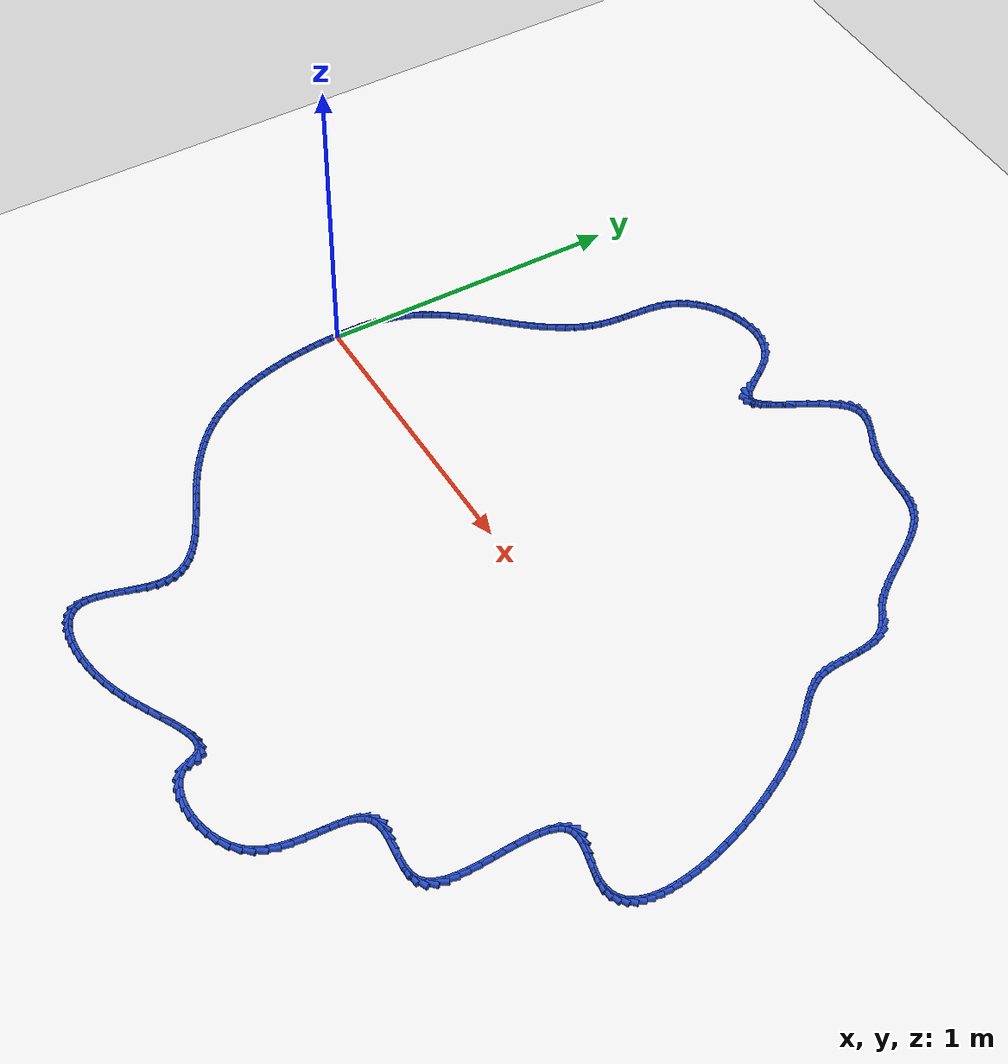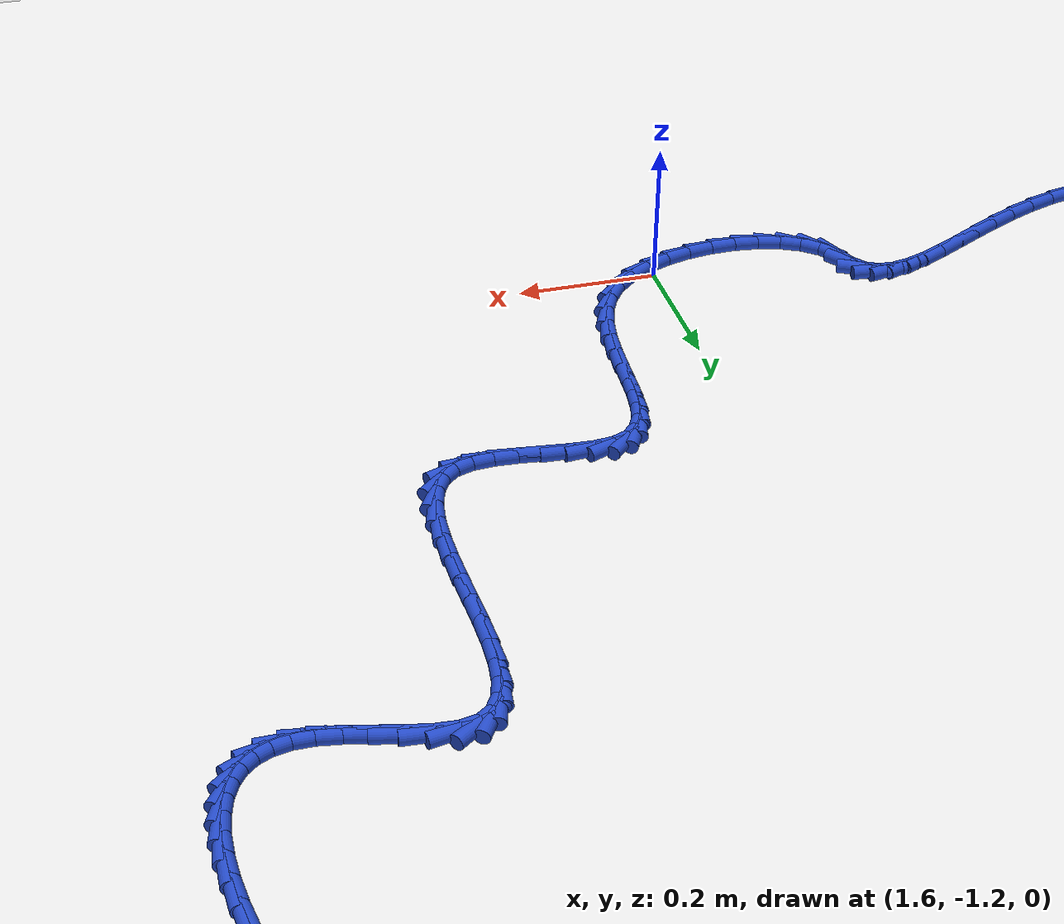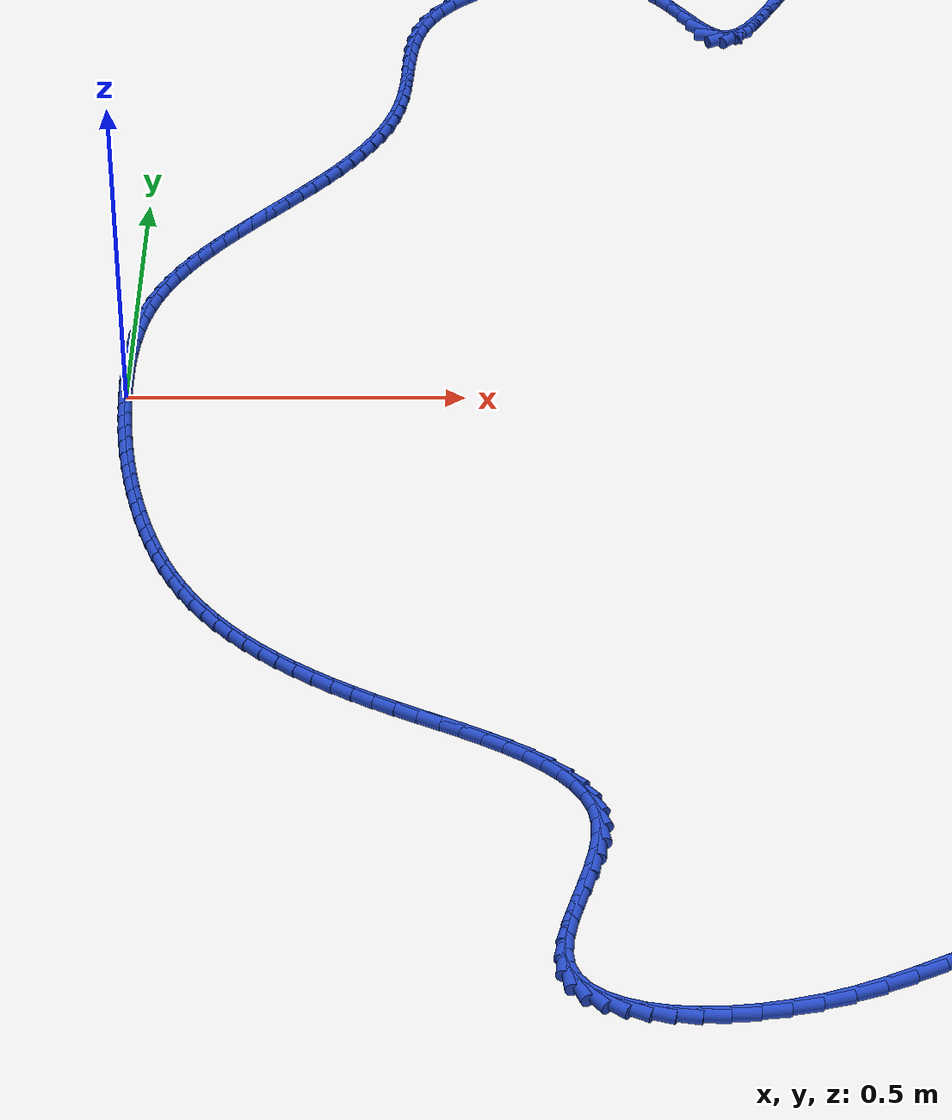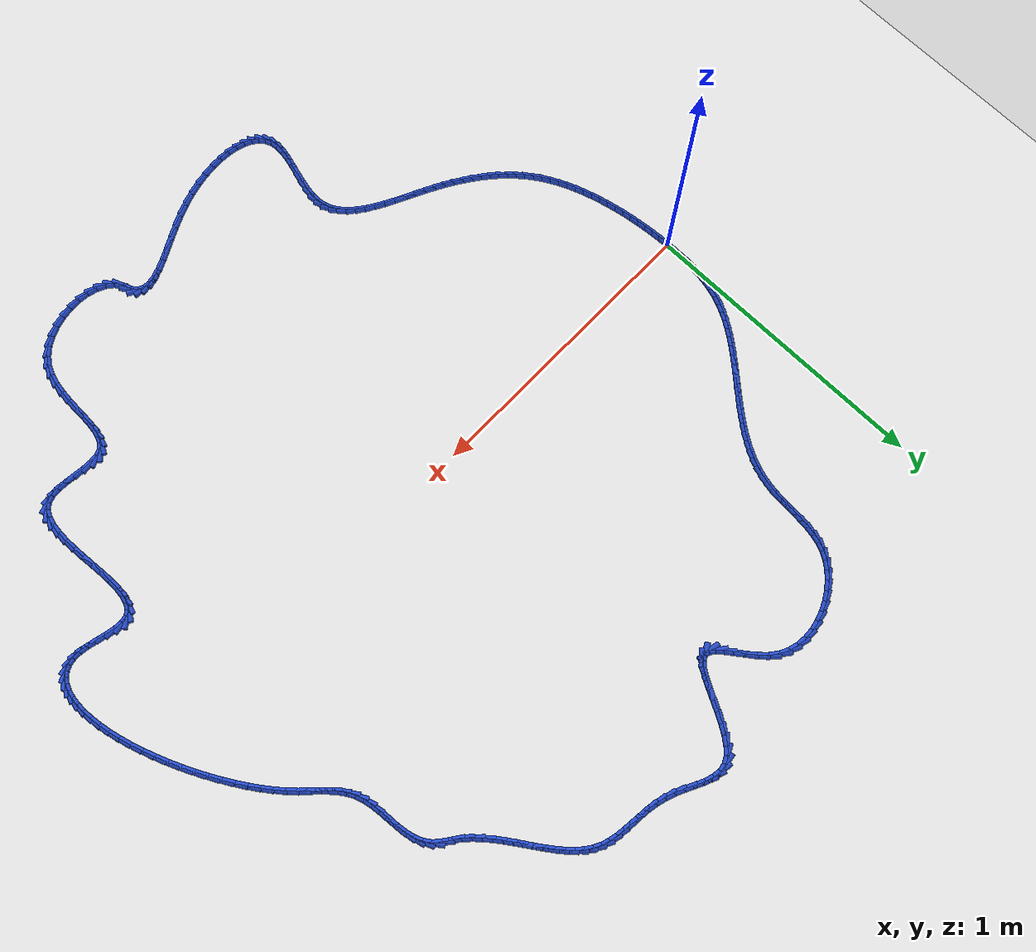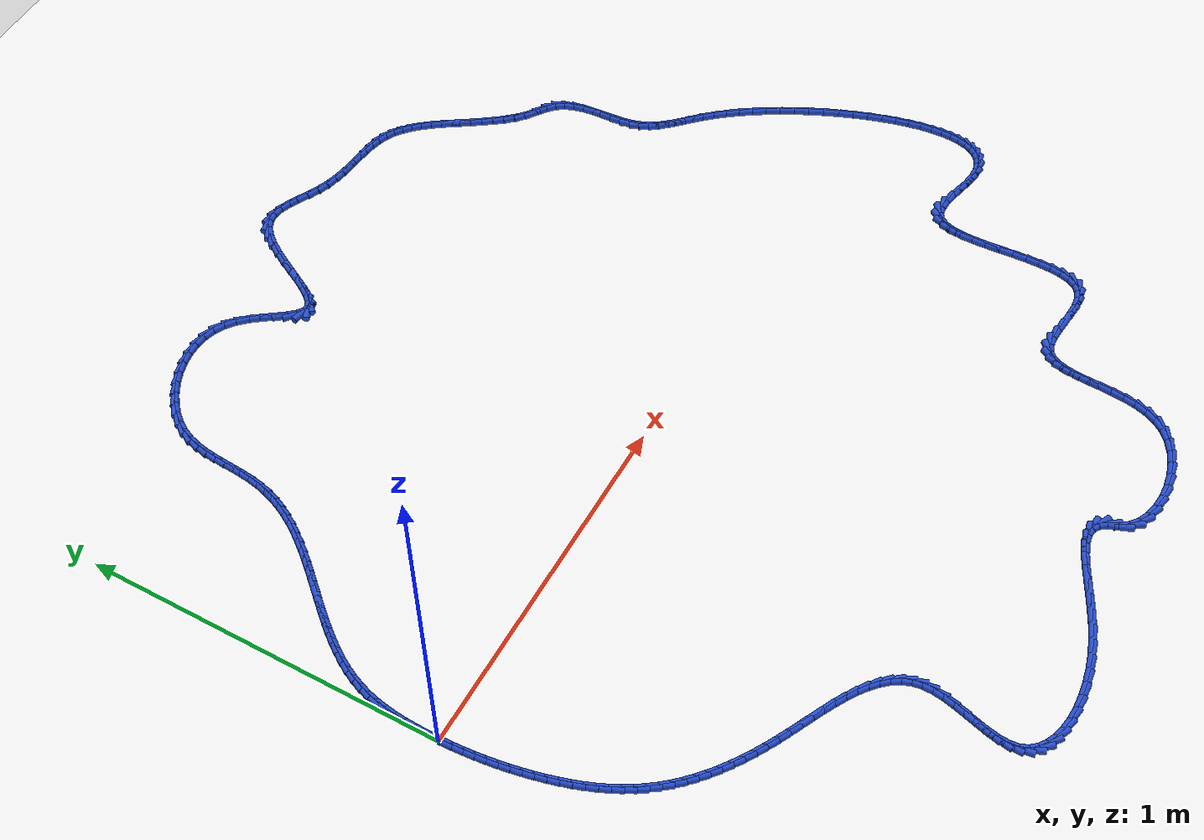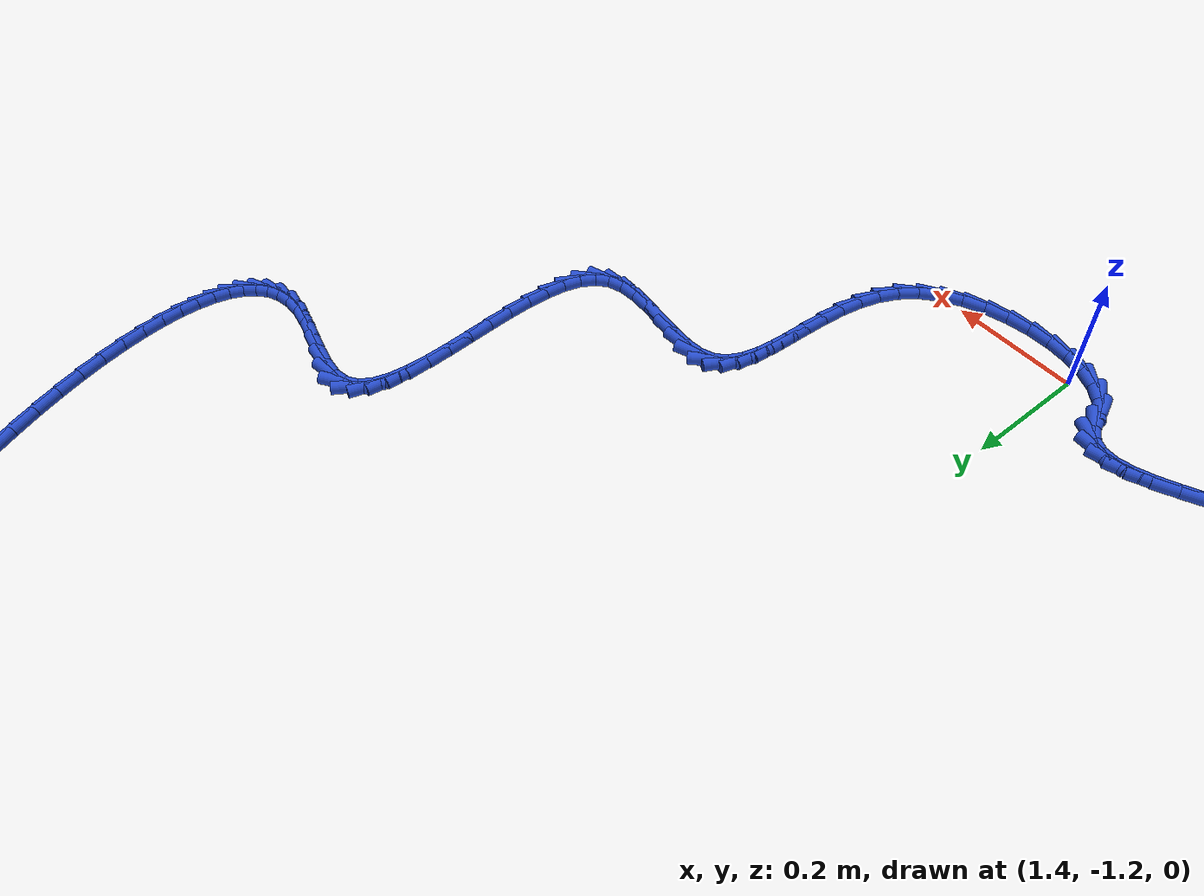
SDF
<sdf version="1.6">
 <world name="default">
  <light name="sun" type="directional">
   <pose>0 0 10 0 -0 0</pose>
   <diffuse>0.8 0.8 0.8 1</diffuse>
   <specular>0.2 0.2 0.2 1</specular>
   <attenuation>
    <range>1000</range>
    <constant>0.9</constant>
    <linear>0.01</linear>
    <quadratic>0.001</quadratic>
   </attenuation>
   <direction>-0.5 0.1 -0.9</direction>
  </light>
  <model name="ground_plane">
   <static>1</static>
   <link name="link">
    <collision name="collision">
     <geometry><plane><normal>0 0 1</normal><size>100 100</size></plane></geometry>
     <surface><friction><ode><mu>100</mu><mu2>50</mu2></ode></friction></surface>
    </collision>
    <visual name="visual">
     <cast_shadows>0</cast_shadows>
     <geometry><plane><normal>0 0 1</normal><size>100 100</size></plane></geometry>
     <material>
      <script><uri>file://media/materials/scripts/gazebo.material</uri><name>Gazebo/WhiteGlow</name></script>
     </material>
    </visual>
   </link>
  </model>
  <gravity>0 0 -9.8</gravity>
  <magnetic_field>6e-06 2.3e-05 -4.2e-05</magnetic_field>
  <atmosphere type="adiabatic"/>
  <physics name="default_physics" default="0" type="ode">
   <max_step_size>0.001</max_step_size>
   <real_time_factor>1</real_time_factor>
   <real_time_update_rate>1000</real_time_update_rate>
  </physics>
  <scene><ambient>0.4 0.4 0.4 1</ambient><background>0.7 0.7 0.7 1</background><shadows>1</shadows></scene>
  <spherical_coordinates>
   <surface_model>EARTH_WGS84</surface_model>
   <latitude_deg>0</latitude_deg>
   <longitude_deg>0</longitude_deg>
   <elevation>0</elevation>
   <heading_deg>0</heading_deg>
  </spherical_coordinates>
  <model name="line">
   <link name="link_0">
    <pose>5.637851296924623e-18 -6.938893903907228e-18 0.01 0 1.57 -1.5538088194006352</pose>
    <collision name="collision">
     <geometry><cylinder><radius>0.01</radius><length>0.08</length></cylinder></geometry>
    </collision>
    <visual name="visual">
     <material>
      <script><name>Gazebo/Blue</name><uri>file://media/materials/scripts/gazebo.material</uri></script>
     </material>
     <geometry><cylinder><radius>0.01</radius><length>0.08</length></cylinder></geometry>
    </visual>
   </link>
   <link name="link_1">
    <pose>-0.0005110091143865744 0.030078571664121947 0.01 0 1.57 1.5618037818562898</pose>
    <collision name="collision">
     <geometry><cylinder><radius>0.01</radius><length>0.08</length></cylinder></geometry>
    </collision>
    <visual name="visual">
     <material>
      <script><name>Gazebo/Blue</name><uri>file://media/materials/scripts/gazebo.material</uri></script>
     </material>
     <geometry><cylinder><radius>0.01</radius><length>0.08</length></cylinder></geometry>
    </visual>
   </link>
   <link name="link_2">
    <pose>-0.0002397270242196615 0.060245201855308496 0.01 0 1.57 1.5294547088791701</pose>
    <collision name="collision">
     <geometry><cylinder><radius>0.01</radius><length>0.08</length></cylinder></geometry>
    </collision>
    <visual name="visual">
     <material>
      <script><name>Gazebo/Blue</name><uri>file://media/materials/scripts/gazebo.material</uri></script>
     </material>
     <geometry><cylinder><radius>0.01</radius><length>0.08</length></cylinder></geometry>
    </visual>
   </link>
   <link name="link_3">
    <pose>0.001005851843149622 0.09035696890232352 0.01 0 1.57 1.4903431412226193</pose>
    <collision name="collision">
     <geometry><cylinder><radius>0.01</radius><length>0.08</length></cylinder></geometry>
    </collision>
    <visual name="visual">
     <material>
      <script><name>Gazebo/Blue</name><uri>file://media/materials/scripts/gazebo.material</uri></script>
     </material>
     <geometry><cylinder><radius>0.01</radius><length>0.08</length></cylinder></geometry>
    </visual>
   </link>
   <link name="link_4">
    <pose>0.0034177330603701425 0.1202709511339308 0.01 0 1.57 1.443993982352836</pose>
    <collision name="collision">
     <geometry><cylinder><radius>0.01</radius><length>0.08</length></cylinder></geometry>
    </collision>
    <visual name="visual">
     <material>
      <script><name>Gazebo/Blue</name><uri>file://media/materials/scripts/gazebo.material</uri></script>
     </material>
     <geometry><cylinder><radius>0.01</radius><length>0.08</length></cylinder></geometry>
    </visual>
   </link>
   <link name="link_5">
    <pose>0.00718792220009077 0.14984422687889418 0.01 0 1.57 1.3898956241181077</pose>
    <collision name="collision">
     <geometry><cylinder><radius>0.01</radius><length>0.08</length></cylinder></geometry>
    </collision>
    <visual name="visual">
     <material>
      <script><name>Gazebo/Blue</name><uri>file://media/materials/scripts/gazebo.material</uri></script>
     </material>
     <geometry><cylinder><radius>0.01</radius><length>0.08</length></cylinder></geometry>
    </visual>
   </link>
   <link name="link_6">
    <pose>0.012508424834960386 0.17893387446597764 0.01 0 1.57 1.3275693930481152</pose>
    <collision name="collision">
     <geometry><cylinder><radius>0.01</radius><length>0.08</length></cylinder></geometry>
    </collision>
    <visual name="visual">
     <material>
      <script><name>Gazebo/Blue</name><uri>file://media/materials/scripts/gazebo.material</uri></script>
     </material>
     <geometry><cylinder><radius>0.01</radius><length>0.08</length></cylinder></geometry>
    </visual>
   </link>
   <link name="link_7">
    <pose>0.019571246537627856 0.20739697222394485 0.01 0 1.57 1.2566828749107217</pose>
    <collision name="collision">
     <geometry><cylinder><radius>0.01</radius><length>0.08</length></cylinder></geometry>
    </collision>
    <visual name="visual">
     <material>
      <script><name>Gazebo/Blue</name><uri>file://media/materials/scripts/gazebo.material</uri></script>
     </material>
     <geometry><cylinder><radius>0.01</radius><length>0.08</length></cylinder></geometry>
    </visual>
   </link>
   <link name="link_8">
    <pose>0.02856810319835885 0.23509076684006391 0.01 0 1.57 1.1812314622817683</pose>
    <collision name="collision">
     <geometry><cylinder><radius>0.01</radius><length>0.08</length></cylinder></geometry>
    </collision>
    <visual name="visual">
     <material>
      <script><name>Gazebo/Blue</name><uri>file://media/materials/scripts/gazebo.material</uri></script>
     </material>
     <geometry><cylinder><radius>0.01</radius><length>0.08</length></cylinder></geometry>
    </visual>
   </link>
   <link name="link_9">
    <pose>0.039587802212604745 0.2619323136791692 0.01 0 1.57 1.111769995521658</pose>
    <collision name="collision">
     <geometry><cylinder><radius>0.01</radius><length>0.08</length></cylinder></geometry>
    </collision>
    <visual name="visual">
     <material>
      <script><name>Gazebo/Blue</name><uri>file://media/materials/scripts/gazebo.material</uri></script>
     </material>
     <geometry><cylinder><radius>0.01</radius><length>0.08</length></cylinder></geometry>
    </visual>
   </link>
   <link name="link_10">
    <pose>0.052464748002979254 0.2879865228133451 0.01 0 1.57 1.0504071157463375</pose>
    <collision name="collision">
     <geometry><cylinder><radius>0.01</radius><length>0.08</length></cylinder></geometry>
    </collision>
    <visual name="visual">
     <material>
      <script><name>Gazebo/Blue</name><uri>file://media/materials/scripts/gazebo.material</uri></script>
     </material>
     <geometry><cylinder><radius>0.01</radius><length>0.08</length></cylinder></geometry>
    </visual>
   </link>
   <link name="link_11">
    <pose>0.06699471870525724 0.3133407532596281 0.01 0 1.57 0.9973610260455834</pose>
    <collision name="collision">
     <geometry><cylinder><radius>0.01</radius><length>0.08</length></cylinder></geometry>
    </collision>
    <visual name="visual">
     <material>
      <script><name>Gazebo/Blue</name><uri>file://media/materials/scripts/gazebo.material</uri></script>
     </material>
     <geometry><cylinder><radius>0.01</radius><length>0.08</length></cylinder></geometry>
    </visual>
   </link>
   <link name="link_12">
    <pose>0.08297349245521338 0.3380823640350544 0.01 0 1.57 0.9525742354037662</pose>
    <collision name="collision">
     <geometry><cylinder><radius>0.01</radius><length>0.08</length></cylinder></geometry>
    </collision>
    <visual name="visual">
     <material>
      <script><name>Gazebo/Blue</name><uri>file://media/materials/scripts/gazebo.material</uri></script>
     </material>
     <geometry><cylinder><radius>0.01</radius><length>0.08</length></cylinder></geometry>
    </visual>
   </link>
   <link name="link_13">
    <pose>0.10019684738862256 0.36229871415666015 0.01 0 1.57 0.9158250410738205</pose>
    <collision name="collision">
     <geometry><cylinder><radius>0.01</radius><length>0.08</length></cylinder></geometry>
    </collision>
    <visual name="visual">
     <material>
      <script><name>Gazebo/Blue</name><uri>file://media/materials/scripts/gazebo.material</uri></script>
     </material>
     <geometry><cylinder><radius>0.01</radius><length>0.08</length></cylinder></geometry>
    </visual>
   </link>
   <link name="link_14">
    <pose>0.11846056164125954 0.3860771626414817 0.01 0 1.57 0.8868190816384095</pose>
    <collision name="collision">
     <geometry><cylinder><radius>0.01</radius><length>0.08</length></cylinder></geometry>
    </collision>
    <visual name="visual">
     <material>
      <script><name>Gazebo/Blue</name><uri>file://media/materials/scripts/gazebo.material</uri></script>
     </material>
     <geometry><cylinder><radius>0.01</radius><length>0.08</length></cylinder></geometry>
    </visual>
   </link>
   <link name="link_15">
    <pose>0.13756041334889899 0.409505068506555 0.01 0 1.57 0.8652567747027111</pose>
    <collision name="collision">
     <geometry><cylinder><radius>0.01</radius><length>0.08</length></cylinder></geometry>
    </collision>
    <visual name="visual">
     <material>
      <script><name>Gazebo/Blue</name><uri>file://media/materials/scripts/gazebo.material</uri></script>
     </material>
     <geometry><cylinder><radius>0.01</radius><length>0.08</length></cylinder></geometry>
    </visual>
   </link>
   <link name="link_16">
    <pose>0.1572921806473159 0.43266979076891665 0.01 0 1.57 0.8508790209512644</pose>
    <collision name="collision">
     <geometry><cylinder><radius>0.01</radius><length>0.08</length></cylinder></geometry>
    </collision>
    <visual name="visual">
     <material>
      <script><name>Gazebo/Blue</name><uri>file://media/materials/scripts/gazebo.material</uri></script>
     </material>
     <geometry><cylinder><radius>0.01</radius><length>0.08</length></cylinder></geometry>
    </visual>
   </link>
   <link name="link_17">
    <pose>0.177451641672285 0.45565868844560276 0.01 0 1.57 0.8434959130607775</pose>
    <collision name="collision">
     <geometry><cylinder><radius>0.01</radius><length>0.08</length></cylinder></geometry>
    </collision>
    <visual name="visual">
     <material>
      <script><name>Gazebo/Blue</name><uri>file://media/materials/scripts/gazebo.material</uri></script>
     </material>
     <geometry><cylinder><radius>0.01</radius><length>0.08</length></cylinder></geometry>
    </visual>
   </link>
   <link name="link_18">
    <pose>0.19783457455958095 0.4785591205536494 0.01 0 1.57 0.8430030838195619</pose>
    <collision name="collision">
     <geometry><cylinder><radius>0.01</radius><length>0.08</length></cylinder></geometry>
    </collision>
    <visual name="visual">
     <material>
      <script><name>Gazebo/Blue</name><uri>file://media/materials/scripts/gazebo.material</uri></script>
     </material>
     <geometry><cylinder><radius>0.01</radius><length>0.08</length></cylinder></geometry>
    </visual>
   </link>
   <link name="link_19">
    <pose>0.21823675744497867 0.5014584461100929 0.01 0 1.57 0.8493891083745766</pose>
    <collision name="collision">
     <geometry><cylinder><radius>0.01</radius><length>0.08</length></cylinder></geometry>
    </collision>
    <visual name="visual">
     <material>
      <script><name>Gazebo/Blue</name><uri>file://media/materials/scripts/gazebo.material</uri></script>
     </material>
     <geometry><cylinder><radius>0.01</radius><length>0.08</length></cylinder></geometry>
    </visual>
   </link>
   <link name="link_20">
    <pose>0.2384539684642528 0.5244440241319694 0.01 0 1.57 0.8627357819041892</pose>
    <collision name="collision">
     <geometry><cylinder><radius>0.01</radius><length>0.08</length></cylinder></geometry>
    </collision>
    <visual name="visual">
     <material>
      <script><name>Gazebo/Blue</name><uri>file://media/materials/scripts/gazebo.material</uri></script>
     </material>
     <geometry><cylinder><radius>0.01</radius><length>0.08</length></cylinder></geometry>
    </visual>
   </link>
   <link name="link_21">
    <pose>0.2582819857531784 0.5476032136363154 0.01 0 1.57 0.8832114266778436</pose>
    <collision name="collision">
     <geometry><cylinder><radius>0.01</radius><length>0.08</length></cylinder></geometry>
    </collision>
    <visual name="visual">
     <material>
      <script><name>Gazebo/Blue</name><uri>file://media/materials/scripts/gazebo.material</uri></script>
     </material>
     <geometry><cylinder><radius>0.01</radius><length>0.08</length></cylinder></geometry>
    </visual>
   </link>
   <link name="link_22">
    <pose>0.27751658744753005 0.5710233736401669 0.01 0 1.57 0.9110557253843615</pose>
    <collision name="collision">
     <geometry><cylinder><radius>0.01</radius><length>0.08</length></cylinder></geometry>
    </collision>
    <visual name="visual">
     <material>
      <script><name>Gazebo/Blue</name><uri>file://media/materials/scripts/gazebo.material</uri></script>
     </material>
     <geometry><cylinder><radius>0.01</radius><length>0.08</length></cylinder></geometry>
    </visual>
   </link>
   <link name="link_23">
    <pose>0.2959535516830825 0.5947918631605601 0.01 0 1.57 0.9465529997581341</pose>
    <collision name="collision">
     <geometry><cylinder><radius>0.01</radius><length>0.08</length></cylinder></geometry>
    </collision>
    <visual name="visual">
     <material>
      <script><name>Gazebo/Blue</name><uri>file://media/materials/scripts/gazebo.material</uri></script>
     </material>
     <geometry><cylinder><radius>0.01</radius><length>0.08</length></cylinder></geometry>
    </visual>
   </link>
   <link name="link_24">
    <pose>0.3133886565956107 0.6189960412145313 0.01 0 1.57 0.9899896044578546</pose>
    <collision name="collision">
     <geometry><cylinder><radius>0.01</radius><length>0.08</length></cylinder></geometry>
    </collision>
    <visual name="visual">
     <material>
      <script><name>Gazebo/Blue</name><uri>file://media/materials/scripts/gazebo.material</uri></script>
     </material>
     <geometry><cylinder><radius>0.01</radius><length>0.08</length></cylinder></geometry>
    </visual>
   </link>
   <link name="link_25">
    <pose>0.3296176803208894 0.6437232668191168 0.01 0 1.57 1.041590828028233</pose>
    <collision name="collision">
     <geometry><cylinder><radius>0.01</radius><length>0.08</length></cylinder></geometry>
    </collision>
    <visual name="visual">
     <material>
      <script><name>Gazebo/Blue</name><uri>file://media/materials/scripts/gazebo.material</uri></script>
     </material>
     <geometry><cylinder><radius>0.01</radius><length>0.08</length></cylinder></geometry>
    </visual>
   </link>
   <link name="link_26">
    <pose>0.34443640099469325 0.6690608989913528 0.01 0 1.57 1.1014345891142463</pose>
    <collision name="collision">
     <geometry><cylinder><radius>0.01</radius><length>0.08</length></cylinder></geometry>
    </collision>
    <visual name="visual">
     <material>
      <script><name>Gazebo/Blue</name><uri>file://media/materials/scripts/gazebo.material</uri></script>
     </material>
     <geometry><cylinder><radius>0.01</radius><length>0.08</length></cylinder></geometry>
    </visual>
   </link>
   <link name="link_27">
    <pose>0.35764059675279725 0.6950962967482754 0.01 0 1.57 1.169344924488211</pose>
    <collision name="collision">
     <geometry><cylinder><radius>0.01</radius><length>0.08</length></cylinder></geometry>
    </collision>
    <visual name="visual">
     <material>
      <script><name>Gazebo/Blue</name><uri>file://media/materials/scripts/gazebo.material</uri></script>
     </material>
     <geometry><cylinder><radius>0.01</radius><length>0.08</length></cylinder></geometry>
    </visual>
   </link>
   <link name="link_28">
    <pose>0.36902604573097597 0.7219168191069211 0.01 0 1.57 1.244764193914915</pose>
    <collision name="collision">
     <geometry><cylinder><radius>0.01</radius><length>0.08</length></cylinder></geometry>
    </collision>
    <visual name="visual">
     <material>
      <script><name>Gazebo/Blue</name><uri>file://media/materials/scripts/gazebo.material</uri></script>
     </material>
     <geometry><cylinder><radius>0.01</radius><length>0.08</length></cylinder></geometry>
    </visual>
   </link>
   <link name="link_29">
    <pose>0.3783888956829555 0.7496095726739407 0.01 0 1.57 1.3223368122751318</pose>
    <collision name="collision">
     <geometry><cylinder><radius>0.01</radius><length>0.08</length></cylinder></geometry>
    </collision>
    <visual name="visual">
     <material>
      <script><name>Gazebo/Blue</name><uri>file://media/materials/scripts/gazebo.material</uri></script>
     </material>
     <geometry><cylinder><radius>0.01</radius><length>0.08</length></cylinder></geometry>
    </visual>
   </link>
   <link name="link_30">
    <pose>0.38563838511574894 0.7781844349049406 0.01 0 1.57 1.3911572000497914</pose>
    <collision name="collision">
     <geometry><cylinder><radius>0.01</radius><length>0.08</length></cylinder></geometry>
    </collision>
    <visual name="visual">
     <material>
      <script><name>Gazebo/Blue</name><uri>file://media/materials/scripts/gazebo.material</uri></script>
     </material>
     <geometry><cylinder><radius>0.01</radius><length>0.08</length></cylinder></geometry>
    </visual>
   </link>
   <link name="link_31">
    <pose>0.3909557389757474 0.8074655449772111 0.01 0 1.57 1.4499399673393059</pose>
    <collision name="collision">
     <geometry><cylinder><radius>0.01</radius><length>0.08</length></cylinder></geometry>
    </collision>
    <visual name="visual">
     <material>
      <script><name>Gazebo/Blue</name><uri>file://media/materials/scripts/gazebo.material</uri></script>
     </material>
     <geometry><cylinder><radius>0.01</radius><length>0.08</length></cylinder></geometry>
    </visual>
   </link>
   <link name="link_32">
    <pose>0.3945729398656215 0.8372494345035162 0.01 0 1.57 1.4906707065102616</pose>
    <collision name="collision">
     <geometry><cylinder><radius>0.01</radius><length>0.08</length></cylinder></geometry>
    </collision>
    <visual name="visual">
     <material>
      <script><name>Gazebo/Blue</name><uri>file://media/materials/scripts/gazebo.material</uri></script>
     </material>
     <geometry><cylinder><radius>0.01</radius><length>0.08</length></cylinder></geometry>
    </visual>
   </link>
   <link name="link_33">
    <pose>0.396988040617587 0.8673263327755523 0.01 0 1.57 1.5049395389462195</pose>
    <collision name="collision">
     <geometry><cylinder><radius>0.01</radius><length>0.08</length></cylinder></geometry>
    </collision>
    <visual name="visual">
     <material>
      <script><name>Gazebo/Blue</name><uri>file://media/materials/scripts/gazebo.material</uri></script>
     </material>
     <geometry><cylinder><radius>0.01</radius><length>0.08</length></cylinder></geometry>
    </visual>
   </link>
   <link name="link_34">
    <pose>0.39897673311417453 0.8974798927369627 0.01 0 1.57 1.492624940425134</pose>
    <collision name="collision">
     <geometry><cylinder><radius>0.01</radius><length>0.08</length></cylinder></geometry>
    </collision>
    <visual name="visual">
     <material>
      <script><name>Gazebo/Blue</name><uri>file://media/materials/scripts/gazebo.material</uri></script>
     </material>
     <geometry><cylinder><radius>0.01</radius><length>0.08</length></cylinder></geometry>
    </visual>
   </link>
   <link name="link_35">
    <pose>0.40132772594029864 0.927493459008894 0.01 0 1.57 1.4532568165698665</pose>
    <collision name="collision">
     <geometry><cylinder><radius>0.01</radius><length>0.08</length></cylinder></geometry>
    </collision>
    <visual name="visual">
     <material>
      <script><name>Gazebo/Blue</name><uri>file://media/materials/scripts/gazebo.material</uri></script>
     </material>
     <geometry><cylinder><radius>0.01</radius><length>0.08</length></cylinder></geometry>
    </visual>
   </link>
   <link name="link_36">
    <pose>0.40482972768087394 0.9571503762124933 0.01 0 1.57 1.3858289965185158</pose>
    <collision name="collision">
     <geometry><cylinder><radius>0.01</radius><length>0.08</length></cylinder></geometry>
    </collision>
    <visual name="visual">
     <material>
      <script><name>Gazebo/Blue</name><uri>file://media/materials/scripts/gazebo.material</uri></script>
     </material>
     <geometry><cylinder><radius>0.01</radius><length>0.08</length></cylinder></geometry>
    </visual>
   </link>
   <link name="link_37">
    <pose>0.4102714469208147 0.9862339889689059 0.01 0 1.57 1.289680802735764</pose>
    <collision name="collision">
     <geometry><cylinder><radius>0.01</radius><length>0.08</length></cylinder></geometry>
    </collision>
    <visual name="visual">
     <material>
      <script><name>Gazebo/Blue</name><uri>file://media/materials/scripts/gazebo.material</uri></script>
     </material>
     <geometry><cylinder><radius>0.01</radius><length>0.08</length></cylinder></geometry>
    </visual>
   </link>
   <link name="link_38">
    <pose>0.4184415922450355 1.014527641899279 0.01 0 1.57 1.166126387622552</pose>
    <collision name="collision">
     <geometry><cylinder><radius>0.01</radius><length>0.08</length></cylinder></geometry>
    </collision>
    <visual name="visual">
     <material>
      <script><name>Gazebo/Blue</name><uri>file://media/materials/scripts/gazebo.material</uri></script>
     </material>
     <geometry><cylinder><radius>0.01</radius><length>0.08</length></cylinder></geometry>
    </visual>
   </link>
   <link name="link_39">
    <pose>0.43012887223845064 1.0418146796247583 0.01 0 1.57 1.021718159743225</pose>
    <collision name="collision">
     <geometry><cylinder><radius>0.01</radius><length>0.08</length></cylinder></geometry>
    </collision>
    <visual name="visual">
     <material>
      <script><name>Gazebo/Blue</name><uri>file://media/materials/scripts/gazebo.material</uri></script>
     </material>
     <geometry><cylinder><radius>0.01</radius><length>0.08</length></cylinder></geometry>
    </visual>
   </link>
   <link name="link_40">
    <pose>0.4460710485726541 1.0678709024240025 0.01 0 1.57 0.8816059710161478</pose>
    <collision name="collision">
     <geometry><cylinder><radius>0.01</radius><length>0.08</length></cylinder></geometry>
    </collision>
    <visual name="visual">
     <material>
      <script><name>Gazebo/Blue</name><uri>file://media/materials/scripts/gazebo.material</uri></script>
     </material>
     <geometry><cylinder><radius>0.01</radius><length>0.08</length></cylinder></geometry>
    </visual>
   </link>
   <link name="link_41">
    <pose>0.4662495672594686 1.0923601135184435 0.01 0 1.57 0.7569735497013308</pose>
    <collision name="collision">
     <geometry><cylinder><radius>0.01</radius><length>0.08</length></cylinder></geometry>
    </collision>
    <visual name="visual">
     <material>
      <script><name>Gazebo/Blue</name><uri>file://media/materials/scripts/gazebo.material</uri></script>
     </material>
     <geometry><cylinder><radius>0.01</radius><length>0.08</length></cylinder></geometry>
    </visual>
   </link>
   <link name="link_42">
    <pose>0.4900667150944571 1.114860352828109 0.01 0 1.57 0.6424183129022573</pose>
    <collision name="collision">
     <geometry><cylinder><radius>0.01</radius><length>0.08</length></cylinder></geometry>
    </collision>
    <visual name="visual">
     <material>
      <script><name>Gazebo/Blue</name><uri>file://media/materials/scripts/gazebo.material</uri></script>
     </material>
     <geometry><cylinder><radius>0.01</radius><length>0.08</length></cylinder></geometry>
    </visual>
   </link>
   <link name="link_43">
    <pose>0.5169100562298813 1.1349474801082984 0.01 0 1.57 0.5327345462630801</pose>
    <collision name="collision">
     <geometry><cylinder><radius>0.01</radius><length>0.08</length></cylinder></geometry>
    </collision>
    <visual name="visual">
     <material>
      <script><name>Gazebo/Blue</name><uri>file://media/materials/scripts/gazebo.material</uri></script>
     </material>
     <geometry><cylinder><radius>0.01</radius><length>0.08</length></cylinder></geometry>
    </visual>
   </link>
   <link name="link_44">
    <pose>0.5461671548180029 1.1521973551143123 0.01 0 1.57 0.4231803610204229</pose>
    <collision name="collision">
     <geometry><cylinder><radius>0.01</radius><length>0.08</length></cylinder></geometry>
    </collision>
    <visual name="visual">
     <material>
      <script><name>Gazebo/Blue</name><uri>file://media/materials/scripts/gazebo.material</uri></script>
     </material>
     <geometry><cylinder><radius>0.01</radius><length>0.08</length></cylinder></geometry>
    </visual>
   </link>
   <link name="link_45">
    <pose>0.5772255750110832 1.1661858376014507 0.01 0 1.57 0.30924750717978405</pose>
    <collision name="collision">
     <geometry><cylinder><radius>0.01</radius><length>0.08</length></cylinder></geometry>
    </collision>
    <visual name="visual">
     <material>
      <script><name>Gazebo/Blue</name><uri>file://media/materials/scripts/gazebo.material</uri></script>
     </material>
     <geometry><cylinder><radius>0.01</radius><length>0.08</length></cylinder></geometry>
    </visual>
   </link>
   <link name="link_46">
    <pose>0.6094728809613835 1.1764887873250123 0.01 0 1.57 0.18649029162062186</pose>
    <collision name="collision">
     <geometry><cylinder><radius>0.01</radius><length>0.08</length></cylinder></geometry>
    </collision>
    <visual name="visual">
     <material>
      <script><name>Gazebo/Blue</name><uri>file://media/materials/scripts/gazebo.material</uri></script>
     </material>
     <geometry><cylinder><radius>0.01</radius><length>0.08</length></cylinder></geometry>
    </visual>
   </link>
   <link name="link_47">
    <pose>0.6422966368211661 1.1826820640402986 0.01 0 1.57 0.050569120087990124</pose>
    <collision name="collision">
     <geometry><cylinder><radius>0.01</radius><length>0.08</length></cylinder></geometry>
    </collision>
    <visual name="visual">
     <material>
      <script><name>Gazebo/Blue</name><uri>file://media/materials/scripts/gazebo.material</uri></script>
     </material>
     <geometry><cylinder><radius>0.01</radius><length>0.08</length></cylinder></geometry>
    </visual>
   </link>
   <link name="link_48">
    <pose>0.6750844067426921 1.1843415275026088 0.01 0 1.57 -0.10227281391559402</pose>
    <collision name="collision">
     <geometry><cylinder><radius>0.01</radius><length>0.08</length></cylinder></geometry>
    </collision>
    <visual name="visual">
     <material>
      <script><name>Gazebo/Blue</name><uri>file://media/materials/scripts/gazebo.material</uri></script>
     </material>
     <geometry><cylinder><radius>0.01</radius><length>0.08</length></cylinder></geometry>
    </visual>
   </link>
   <link name="link_49">
    <pose>0.7072237548782232 1.1810430374672423 0.01 0 1.57 -0.2740476525816257</pose>
    <collision name="collision">
     <geometry><cylinder><radius>0.01</radius><length>0.08</length></cylinder></geometry>
    </collision>
    <visual name="visual">
     <material>
      <script><name>Gazebo/Blue</name><uri>file://media/materials/scripts/gazebo.material</uri></script>
     </material>
     <geometry><cylinder><radius>0.01</radius><length>0.08</length></cylinder></geometry>
    </visual>
   </link>
   <link name="link_50">
    <pose>0.7381022453800211 1.1723624536894999 0.01 0 1.57 -0.46321226137972576</pose>
    <collision name="collision">
     <geometry><cylinder><radius>0.01</radius><length>0.08</length></cylinder></geometry>
    </collision>
    <visual name="visual">
     <material>
      <script><name>Gazebo/Blue</name><uri>file://media/materials/scripts/gazebo.material</uri></script>
     </material>
     <geometry><cylinder><radius>0.01</radius><length>0.08</length></cylinder></geometry>
    </visual>
   </link>
   <link name="link_51">
    <pose>0.767107442400347 1.1578756359246811 0.01 0 1.57 -0.6604622022857236</pose>
    <collision name="collision">
     <geometry><cylinder><radius>0.01</radius><length>0.08</length></cylinder></geometry>
    </collision>
    <visual name="visual">
     <material>
      <script><name>Gazebo/Blue</name><uri>file://media/materials/scripts/gazebo.material</uri></script>
     </material>
     <geometry><cylinder><radius>0.01</radius><length>0.08</length></cylinder></geometry>
    </visual>
   </link>
   <link name="link_52">
    <pose>0.793657213112827 1.13725055849826 0.01 0 1.57 -0.8162864137049751</pose>
    <collision name="collision">
     <geometry><cylinder><radius>0.01</radius><length>0.08</length></cylinder></geometry>
    </collision>
    <visual name="visual">
     <material>
      <script><name>Gazebo/Blue</name><uri>file://media/materials/scripts/gazebo.material</uri></script>
     </material>
     <geometry><cylinder><radius>0.01</radius><length>0.08</length></cylinder></geometry>
    </visual>
   </link>
   <link name="link_53">
    <pose>0.8176772441910467 1.1116988561649102 0.01 0 1.57 -0.908229339026705</pose>
    <collision name="collision">
     <geometry><cylinder><radius>0.01</radius><length>0.08</length></cylinder></geometry>
    </collision>
    <visual name="visual">
     <material>
      <script><name>Gazebo/Blue</name><uri>file://media/materials/scripts/gazebo.material</uri></script>
     </material>
     <geometry><cylinder><radius>0.01</radius><length>0.08</length></cylinder></geometry>
    </visual>
   </link>
   <link name="link_54">
    <pose>0.839513976861812 1.0837111656756095 0.01 0 1.57 -0.9484617701473832</pose>
    <collision name="collision">
     <geometry><cylinder><radius>0.01</radius><length>0.08</length></cylinder></geometry>
    </collision>
    <visual name="visual">
     <material>
      <script><name>Gazebo/Blue</name><uri>file://media/materials/scripts/gazebo.material</uri></script>
     </material>
     <geometry><cylinder><radius>0.01</radius><length>0.08</length></cylinder></geometry>
    </visual>
   </link>
   <link name="link_55">
    <pose>0.8595265490714579 1.055816719037168 0.01 0 1.57 -0.9376675126594138</pose>
    <collision name="collision">
     <geometry><cylinder><radius>0.01</radius><length>0.08</length></cylinder></geometry>
    </collision>
    <visual name="visual">
     <material>
      <script><name>Gazebo/Blue</name><uri>file://media/materials/scripts/gazebo.material</uri></script>
     </material>
     <geometry><cylinder><radius>0.01</radius><length>0.08</length></cylinder></geometry>
    </visual>
   </link>
   <link name="link_56">
    <pose>0.8780740987663186 1.0305447482563952 0.01 0 1.57 -0.856589159546551</pose>
    <collision name="collision">
     <geometry><cylinder><radius>0.01</radius><length>0.08</length></cylinder></geometry>
    </collision>
    <visual name="visual">
     <material>
      <script><name>Gazebo/Blue</name><uri>file://media/materials/scripts/gazebo.material</uri></script>
     </material>
     <geometry><cylinder><radius>0.01</radius><length>0.08</length></cylinder></geometry>
    </visual>
   </link>
   <link name="link_57">
    <pose>0.8955157638927299 1.0104244853401017 0.01 0 1.57 -0.6403553867307327</pose>
    <collision name="collision">
     <geometry><cylinder><radius>0.01</radius><length>0.08</length></cylinder></geometry>
    </collision>
    <visual name="visual">
     <material>
      <script><name>Gazebo/Blue</name><uri>file://media/materials/scripts/gazebo.material</uri></script>
     </material>
     <geometry><cylinder><radius>0.01</radius><length>0.08</length></cylinder></geometry>
    </visual>
   </link>
   <link name="link_58">
    <pose>0.9122106823970259 0.997985162295097 0.01 0 1.57 -0.14150135525549745</pose>
    <collision name="collision">
     <geometry><cylinder><radius>0.01</radius><length>0.08</length></cylinder></geometry>
    </collision>
    <visual name="visual">
     <material>
      <script><name>Gazebo/Blue</name><uri>file://media/materials/scripts/gazebo.material</uri></script>
     </material>
     <geometry><cylinder><radius>0.01</radius><length>0.08</length></cylinder></geometry>
    </visual>
   </link>
   <link name="link_59">
    <pose>0.9285136425683247 0.9956627503383902 0.01 0 1.57 0.4659154382653027</pose>
    <collision name="collision">
     <geometry><cylinder><radius>0.01</radius><length>0.08</length></cylinder></geometry>
    </collision>
    <visual name="visual">
     <material>
      <script><name>Gazebo/Blue</name><uri>file://media/materials/scripts/gazebo.material</uri></script>
     </material>
     <geometry><cylinder><radius>0.01</radius><length>0.08</length></cylinder></geometry>
    </visual>
   </link>
   <link name="link_60">
    <pose>0.9446814576412832 1.0037925422877454 0.01 0 1.57 0.8050210756424779</pose>
    <collision name="collision">
     <geometry><cylinder><radius>0.01</radius><length>0.08</length></cylinder></geometry>
    </collision>
    <visual name="visual">
     <material>
      <script><name>Gazebo/Blue</name><uri>file://media/materials/scripts/gazebo.material</uri></script>
     </material>
     <geometry><cylinder><radius>0.01</radius><length>0.08</length></cylinder></geometry>
    </visual>
   </link>
   <link name="link_61">
    <pose>0.9608741005876147 1.0206334835716706 0.01 0 1.57 0.9666791874586514</pose>
    <collision name="collision">
     <geometry><cylinder><radius>0.01</radius><length>0.08</length></cylinder></geometry>
    </collision>
    <visual name="visual">
     <material>
      <script><name>Gazebo/Blue</name><uri>file://media/materials/scripts/gazebo.material</uri></script>
     </material>
     <geometry><cylinder><radius>0.01</radius><length>0.08</length></cylinder></geometry>
    </visual>
   </link>
   <link name="link_62">
    <pose>0.9772474216897759 1.0443561252379137 0.01 0 1.57 1.0446819030451595</pose>
    <collision name="collision">
     <geometry><cylinder><radius>0.01</radius><length>0.08</length></cylinder></geometry>
    </collision>
    <visual name="visual">
     <material>
      <script><name>Gazebo/Blue</name><uri>file://media/materials/scripts/gazebo.material</uri></script>
     </material>
     <geometry><cylinder><radius>0.01</radius><length>0.08</length></cylinder></geometry>
    </visual>
   </link>
   <link name="link_63">
    <pose>0.9939572712302231 1.073131018334222 0.01 0 1.57 1.0775166116276274</pose>
    <collision name="collision">
     <geometry><cylinder><radius>0.01</radius><length>0.08</length></cylinder></geometry>
    </collision>
    <visual name="visual">
     <material>
      <script><name>Gazebo/Blue</name><uri>file://media/materials/scripts/gazebo.material</uri></script>
     </material>
     <geometry><cylinder><radius>0.01</radius><length>0.08</length></cylinder></geometry>
    </visual>
   </link>
   <link name="link_64">
    <pose>1.0111594994914133 1.105128713908343 0.01 0 1.57 1.0798626204709945</pose>
    <collision name="collision">
     <geometry><cylinder><radius>0.01</radius><length>0.08</length></cylinder></geometry>
    </collision>
    <visual name="visual">
     <material>
      <script><name>Gazebo/Blue</name><uri>file://media/materials/scripts/gazebo.material</uri></script>
     </material>
     <geometry><cylinder><radius>0.01</radius><length>0.08</length></cylinder></geometry>
    </visual>
   </link>
   <link name="link_65">
    <pose>1.0290099567558029 1.138519763008025 0.01 0 1.57 1.0557053734130493</pose>
    <collision name="collision">
     <geometry><cylinder><radius>0.01</radius><length>0.08</length></cylinder></geometry>
    </collision>
    <visual name="visual">
     <material>
      <script><name>Gazebo/Blue</name><uri>file://media/materials/scripts/gazebo.material</uri></script>
     </material>
     <geometry><cylinder><radius>0.01</radius><length>0.08</length></cylinder></geometry>
    </visual>
   </link>
   <link name="link_66">
    <pose>1.0476644933058474 1.1714747166810144 0.01 0 1.57 1.002101872421107</pose>
    <collision name="collision">
     <geometry><cylinder><radius>0.01</radius><length>0.08</length></cylinder></geometry>
    </collision>
    <visual name="visual">
     <material>
      <script><name>Gazebo/Blue</name><uri>file://media/materials/scripts/gazebo.material</uri></script>
     </material>
     <geometry><cylinder><radius>0.01</radius><length>0.08</length></cylinder></geometry>
    </visual>
   </link>
   <link name="link_67">
    <pose>1.0672789594240037 1.2021641259750593 0.01 0 1.57 0.90868334507961</pose>
    <collision name="collision">
     <geometry><cylinder><radius>0.01</radius><length>0.08</length></cylinder></geometry>
    </collision>
    <visual name="visual">
     <material>
      <script><name>Gazebo/Blue</name><uri>file://media/materials/scripts/gazebo.material</uri></script>
     </material>
     <geometry><cylinder><radius>0.01</radius><length>0.08</length></cylinder></geometry>
    </visual>
   </link>
   <link name="link_68">
    <pose>1.0880092053927293 1.228758541937908 0.01 0 1.57 0.7541956222603117</pose>
    <collision name="collision">
     <geometry><cylinder><radius>0.01</radius><length>0.08</length></cylinder></geometry>
    </collision>
    <visual name="visual">
     <material>
      <script><name>Gazebo/Blue</name><uri>file://media/materials/scripts/gazebo.material</uri></script>
     </material>
     <geometry><cylinder><radius>0.01</radius><length>0.08</length></cylinder></geometry>
    </visual>
   </link>
   <link name="link_69">
    <pose>1.1100110814944801 1.249428515617307 0.01 0 1.57 0.5038236632814386</pose>
    <collision name="collision">
     <geometry><cylinder><radius>0.01</radius><length>0.08</length></cylinder></geometry>
    </collision>
    <visual name="visual">
     <material>
      <script><name>Gazebo/Blue</name><uri>file://media/materials/scripts/gazebo.material</uri></script>
     </material>
     <geometry><cylinder><radius>0.01</radius><length>0.08</length></cylinder></geometry>
    </visual>
   </link>
   <link name="link_70">
    <pose>1.1334404380117116 1.262344598061004 0.01 0 1.57 0.15256358471519296</pose>
    <collision name="collision">
     <geometry><cylinder><radius>0.01</radius><length>0.08</length></cylinder></geometry>
    </collision>
    <visual name="visual">
     <material>
      <script><name>Gazebo/Blue</name><uri>file://media/materials/scripts/gazebo.material</uri></script>
     </material>
     <geometry><cylinder><radius>0.01</radius><length>0.08</length></cylinder></geometry>
    </visual>
   </link>
   <link name="link_71">
    <pose>1.1584089076676634 1.2661837095535098 0.01 0 1.57 -0.1490313379004888</pose>
    <collision name="collision">
     <geometry><cylinder><radius>0.01</radius><length>0.08</length></cylinder></geometry>
    </collision>
    <visual name="visual">
     <material>
      <script><name>Gazebo/Blue</name><uri>file://media/materials/scripts/gazebo.material</uri></script>
     </material>
     <geometry><cylinder><radius>0.01</radius><length>0.08</length></cylinder></geometry>
    </visual>
   </link>
   <link name="link_72">
    <pose>1.1848012346890986 1.262221044839124 0.01 0 1.57 -0.3362950946153062</pose>
    <collision name="collision">
     <geometry><cylinder><radius>0.01</radius><length>0.08</length></cylinder></geometry>
    </collision>
    <visual name="visual">
     <material>
      <script><name>Gazebo/Blue</name><uri>file://media/materials/scripts/gazebo.material</uri></script>
     </material>
     <geometry><cylinder><radius>0.01</radius><length>0.08</length></cylinder></geometry>
    </visual>
   </link>
   <link name="link_73">
    <pose>1.2124295896437536 1.2525628953798391 0.01 0 1.57 -0.4327427645418528</pose>
    <collision name="collision">
     <geometry><cylinder><radius>0.01</radius><length>0.08</length></cylinder></geometry>
    </collision>
    <visual name="visual">
     <material>
      <script><name>Gazebo/Blue</name><uri>file://media/materials/scripts/gazebo.material</uri></script>
     </material>
     <geometry><cylinder><radius>0.01</radius><length>0.08</length></cylinder></geometry>
    </visual>
   </link>
   <link name="link_74">
    <pose>1.2411061107123165 1.239315923526631 0.01 0 1.57 -0.462583129608852</pose>
    <collision name="collision">
     <geometry><cylinder><radius>0.01</radius><length>0.08</length></cylinder></geometry>
    </collision>
    <visual name="visual">
     <material>
      <script><name>Gazebo/Blue</name><uri>file://media/materials/scripts/gazebo.material</uri></script>
     </material>
     <geometry><cylinder><radius>0.01</radius><length>0.08</length></cylinder></geometry>
    </visual>
   </link>
   <link name="link_75">
    <pose>1.2706429360754734 1.2245867916304742 0.01 0 1.57 -0.43681664045512414</pose>
    <collision name="collision">
     <geometry><cylinder><radius>0.01</radius><length>0.08</length></cylinder></geometry>
    </collision>
    <visual name="visual">
     <material>
      <script><name>Gazebo/Blue</name><uri>file://media/materials/scripts/gazebo.material</uri></script>
     </material>
     <geometry><cylinder><radius>0.01</radius><length>0.08</length></cylinder></geometry>
    </visual>
   </link>
   <link name="link_76">
    <pose>1.3008522039139119 1.2104821620423447 0.01 0 1.57 -0.35619898950767165</pose>
    <collision name="collision">
     <geometry><cylinder><radius>0.01</radius><length>0.08</length></cylinder></geometry>
    </collision>
    <visual name="visual">
     <material>
      <script><name>Gazebo/Blue</name><uri>file://media/materials/scripts/gazebo.material</uri></script>
     </material>
     <geometry><cylinder><radius>0.01</radius><length>0.08</length></cylinder></geometry>
    </visual>
   </link>
   <link name="link_77">
    <pose>1.3315447877750008 1.1990623878253266 0.01 0 1.57 -0.2536071368032528</pose>
    <collision name="collision">
     <geometry><cylinder><radius>0.01</radius><length>0.08</length></cylinder></geometry>
    </collision>
    <visual name="visual">
     <material>
      <script><name>Gazebo/Blue</name><uri>file://media/materials/scripts/gazebo.material</uri></script>
     </material>
     <geometry><cylinder><radius>0.01</radius><length>0.08</length></cylinder></geometry>
    </visual>
   </link>
   <link name="link_78">
    <pose>1.3624947688026623 1.1910405303182343 0.01 0 1.57 -0.17393738433878203</pose>
    <collision name="collision">
     <geometry><cylinder><radius>0.01</radius><length>0.08</length></cylinder></geometry>
    </collision>
    <visual name="visual">
     <material>
      <script><name>Gazebo/Blue</name><uri>file://media/materials/scripts/gazebo.material</uri></script>
     </material>
     <geometry><cylinder><radius>0.01</radius><length>0.08</length></cylinder></geometry>
    </visual>
   </link>
   <link name="link_79">
    <pose>1.3934345652022162 1.185604006239557 0.01 0 1.57 -0.1215746584129933</pose>
    <collision name="collision">
     <geometry><cylinder><radius>0.01</radius><length>0.08</length></cylinder></geometry>
    </collision>
    <visual name="visual">
     <material>
      <script><name>Gazebo/Blue</name><uri>file://media/materials/scripts/gazebo.material</uri></script>
     </material>
     <geometry><cylinder><radius>0.01</radius><length>0.08</length></cylinder></geometry>
    </visual>
   </link>
   <link name="link_80">
    <pose>1.424094351716647 1.1818580795274864 0.01 0 1.57 -0.09766471456197072</pose>
    <collision name="collision">
     <geometry><cylinder><radius>0.01</radius><length>0.08</length></cylinder></geometry>
    </collision>
    <visual name="visual">
     <material>
      <script><name>Gazebo/Blue</name><uri>file://media/materials/scripts/gazebo.material</uri></script>
     </material>
     <geometry><cylinder><radius>0.01</radius><length>0.08</length></cylinder></geometry>
    </visual>
   </link>
   <link name="link_81">
    <pose>1.45420430308894 1.1789080141202144 0.01 0 1.57 -0.10372033896821033</pose>
    <collision name="collision">
     <geometry><cylinder><radius>0.01</radius><length>0.08</length></cylinder></geometry>
    </collision>
    <visual name="visual">
     <material>
      <script><name>Gazebo/Blue</name><uri>file://media/materials/scripts/gazebo.material</uri></script>
     </material>
     <geometry><cylinder><radius>0.01</radius><length>0.08</length></cylinder></geometry>
    </visual>
   </link>
   <link name="link_82">
    <pose>1.48349459406208 1.1758590739559318 0.01 0 1.57 -0.14237882392704396</pose>
    <collision name="collision">
     <geometry><cylinder><radius>0.01</radius><length>0.08</length></cylinder></geometry>
    </collision>
    <visual name="visual">
     <material>
      <script><name>Gazebo/Blue</name><uri>file://media/materials/scripts/gazebo.material</uri></script>
     </material>
     <geometry><cylinder><radius>0.01</radius><length>0.08</length></cylinder></geometry>
    </visual>
   </link>
   <link name="link_83">
    <pose>1.5116953993790516 1.171816522972831 0.01 0 1.57 -0.21746584609798453</pose>
    <collision name="collision">
     <geometry><cylinder><radius>0.01</radius><length>0.08</length></cylinder></geometry>
    </collision>
    <visual name="visual">
     <material>
      <script><name>Gazebo/Blue</name><uri>file://media/materials/scripts/gazebo.material</uri></script>
     </material>
     <geometry><cylinder><radius>0.01</radius><length>0.08</length></cylinder></geometry>
    </visual>
   </link>
   <link name="link_84">
    <pose>1.5385368937828403 1.1658856251091032 0.01 0 1.57 -0.3327705297779046</pose>
    <collision name="collision">
     <geometry><cylinder><radius>0.01</radius><length>0.08</length></cylinder></geometry>
    </collision>
    <visual name="visual">
     <material>
      <script><name>Gazebo/Blue</name><uri>file://media/materials/scripts/gazebo.material</uri></script>
     </material>
     <geometry><cylinder><radius>0.01</radius><length>0.08</length></cylinder></geometry>
    </visual>
   </link>
   <link name="link_85">
    <pose>1.563749252016431 1.1571716443029403 0.01 0 1.57 -0.4800742681273775</pose>
    <collision name="collision">
     <geometry><cylinder><radius>0.01</radius><length>0.08</length></cylinder></geometry>
    </collision>
    <visual name="visual">
     <material>
      <script><name>Gazebo/Blue</name><uri>file://media/materials/scripts/gazebo.material</uri></script>
     </material>
     <geometry><cylinder><radius>0.01</radius><length>0.08</length></cylinder></geometry>
    </visual>
   </link>
   <link name="link_86">
    <pose>1.587146399842361 1.1449886267054088 0.01 0 1.57 -0.6177923474465064</pose>
    <collision name="collision">
     <geometry><cylinder><radius>0.01</radius><length>0.08</length></cylinder></geometry>
    </collision>
    <visual name="visual">
     <material>
      <script><name>Gazebo/Blue</name><uri>file://media/materials/scripts/gazebo.material</uri></script>
     </material>
     <geometry><cylinder><radius>0.01</radius><length>0.08</length></cylinder></geometry>
    </visual>
   </link>
   <link name="link_87">
    <pose>1.6088964115444664 1.1295334723403787 0.01 0 1.57 -0.7319729853006509</pose>
    <collision name="collision">
     <geometry><cylinder><radius>0.01</radius><length>0.08</length></cylinder></geometry>
    </collision>
    <visual name="visual">
     <material>
      <script><name>Gazebo/Blue</name><uri>file://media/materials/scripts/gazebo.material</uri></script>
     </material>
     <geometry><cylinder><radius>0.01</radius><length>0.08</length></cylinder></geometry>
    </visual>
   </link>
   <link name="link_88">
    <pose>1.6292609550238453 1.1112363999737151 0.01 0 1.57 -0.8221286787168595</pose>
    <collision name="collision">
     <geometry><cylinder><radius>0.01</radius><length>0.08</length></cylinder></geometry>
    </collision>
    <visual name="visual">
     <material>
      <script><name>Gazebo/Blue</name><uri>file://media/materials/scripts/gazebo.material</uri></script>
     </material>
     <geometry><cylinder><radius>0.01</radius><length>0.08</length></cylinder></geometry>
    </visual>
   </link>
   <link name="link_89">
    <pose>1.6485016987443655 1.0905276297742086 0.01 0 1.57 -0.8900004937260814</pose>
    <collision name="collision">
     <geometry><cylinder><radius>0.01</radius><length>0.08</length></cylinder></geometry>
    </collision>
    <visual name="visual">
     <material>
      <script><name>Gazebo/Blue</name><uri>file://media/materials/scripts/gazebo.material</uri></script>
     </material>
     <geometry><cylinder><radius>0.01</radius><length>0.08</length></cylinder></geometry>
    </visual>
   </link>
   <link name="link_90">
    <pose>1.6668803111698947 1.0678373819106484 0.01 0 1.57 -0.938019441958006</pose>
    <collision name="collision">
     <geometry><cylinder><radius>0.01</radius><length>0.08</length></cylinder></geometry>
    </collision>
    <visual name="visual">
     <material>
      <script><name>Gazebo/Blue</name><uri>file://media/materials/scripts/gazebo.material</uri></script>
     </material>
     <geometry><cylinder><radius>0.01</radius><length>0.08</length></cylinder></geometry>
    </visual>
   </link>
   <link name="link_91">
    <pose>1.6846584607642998 1.0435958765518243 0.01 0 1.57 -0.9684391818790308</pose>
    <collision name="collision">
     <geometry><cylinder><radius>0.01</radius><length>0.08</length></cylinder></geometry>
    </collision>
    <visual name="visual">
     <material>
      <script><name>Gazebo/Blue</name><uri>file://media/materials/scripts/gazebo.material</uri></script>
     </material>
     <geometry><cylinder><radius>0.01</radius><length>0.08</length></cylinder></geometry>
    </visual>
   </link>
   <link name="link_92">
    <pose>1.7020978159914495 1.0182333338665255 0.01 0 1.57 -0.9829711763759497</pose>
    <collision name="collision">
     <geometry><cylinder><radius>0.01</radius><length>0.08</length></cylinder></geometry>
    </collision>
    <visual name="visual">
     <material>
      <script><name>Gazebo/Blue</name><uri>file://media/materials/scripts/gazebo.material</uri></script>
     </material>
     <geometry><cylinder><radius>0.01</radius><length>0.08</length></cylinder></geometry>
    </visual>
   </link>
   <link name="link_93">
    <pose>1.7194600453152111 0.9921799740235417 0.01 0 1.57 -0.9826849676559423</pose>
    <collision name="collision">
     <geometry><cylinder><radius>0.01</radius><length>0.08</length></cylinder></geometry>
    </collision>
    <visual name="visual">
     <material>
      <script><name>Gazebo/Blue</name><uri>file://media/materials/scripts/gazebo.material</uri></script>
     </material>
     <geometry><cylinder><radius>0.01</radius><length>0.08</length></cylinder></geometry>
    </visual>
   </link>
   <link name="link_94">
    <pose>1.7370068171994524 0.965866017191663 0.01 0 1.57 -0.9680220597135583</pose>
    <collision name="collision">
     <geometry><cylinder><radius>0.01</radius><length>0.08</length></cylinder></geometry>
    </collision>
    <visual name="visual">
     <material>
      <script><name>Gazebo/Blue</name><uri>file://media/materials/scripts/gazebo.material</uri></script>
     </material>
     <geometry><cylinder><radius>0.01</radius><length>0.08</length></cylinder></geometry>
    </visual>
   </link>
   <link name="link_95">
    <pose>1.7549998001080407 0.9397216835396787 0.01 0 1.57 -0.9388565867463411</pose>
    <collision name="collision">
     <geometry><cylinder><radius>0.01</radius><length>0.08</length></cylinder></geometry>
    </collision>
    <visual name="visual">
     <material>
      <script><name>Gazebo/Blue</name><uri>file://media/materials/scripts/gazebo.material</uri></script>
     </material>
     <geometry><cylinder><radius>0.01</radius><length>0.08</length></cylinder></geometry>
    </visual>
   </link>
   <link name="link_96">
    <pose>1.7737006625048437 0.9141771932363781 0.01 0 1.57 -0.8945928311818488</pose>
    <collision name="collision">
     <geometry><cylinder><radius>0.01</radius><length>0.08</length></cylinder></geometry>
    </collision>
    <visual name="visual">
     <material>
      <script><name>Gazebo/Blue</name><uri>file://media/materials/scripts/gazebo.material</uri></script>
     </material>
     <geometry><cylinder><radius>0.01</radius><length>0.08</length></cylinder></geometry>
    </visual>
   </link>
   <link name="link_97">
    <pose>1.7933710728537295 0.8896627664505518 0.01 0 1.57 -0.8343291271236721</pose>
    <collision name="collision">
     <geometry><cylinder><radius>0.01</radius><length>0.08</length></cylinder></geometry>
    </collision>
    <visual name="visual">
     <material>
      <script><name>Gazebo/Blue</name><uri>file://media/materials/scripts/gazebo.material</uri></script>
     </material>
     <geometry><cylinder><radius>0.01</radius><length>0.08</length></cylinder></geometry>
    </visual>
   </link>
   <link name="link_98">
    <pose>1.8142726996185656 0.8666086233509885 0.01 0 1.57 -0.7571475396808894</pose>
    <collision name="collision">
     <geometry><cylinder><radius>0.01</radius><length>0.08</length></cylinder></geometry>
    </collision>
    <visual name="visual">
     <material>
      <script><name>Gazebo/Blue</name><uri>file://media/materials/scripts/gazebo.material</uri></script>
     </material>
     <geometry><cylinder><radius>0.01</radius><length>0.08</length></cylinder></geometry>
    </visual>
   </link>
   <link name="link_99">
    <pose>1.8366672112632192 0.8454449841064782 0.01 0 1.57 -0.6636603782006256</pose>
    <collision name="collision">
     <geometry><cylinder><radius>0.01</radius><length>0.08</length></cylinder></geometry>
    </collision>
    <visual name="visual">
     <material>
      <script><name>Gazebo/Blue</name><uri>file://media/materials/scripts/gazebo.material</uri></script>
     </material>
     <geometry><cylinder><radius>0.01</radius><length>0.08</length></cylinder></geometry>
    </visual>
   </link>
   <link name="link_100">
    <pose>1.8607914538881587 0.8265801444571018 0.01 0 1.57 -0.616992772604168</pose>
    <collision name="collision">
     <geometry><cylinder><radius>0.01</radius><length>0.08</length></cylinder></geometry>
    </collision>
    <visual name="visual">
     <material>
      <script><name>Gazebo/Blue</name><uri>file://media/materials/scripts/gazebo.material</uri></script>
     </material>
     <geometry><cylinder><radius>0.01</radius><length>0.08</length></cylinder></geometry>
    </visual>
   </link>
   <link name="link_101">
    <pose>1.8854063956211324 0.8091188263907333 0.01 0 1.57 -0.7208788655949174</pose>
    <collision name="collision">
     <geometry><cylinder><radius>0.01</radius><length>0.08</length></cylinder></geometry>
    </collision>
    <visual name="visual">
     <material>
      <script><name>Gazebo/Blue</name><uri>file://media/materials/scripts/gazebo.material</uri></script>
     </material>
     <geometry><cylinder><radius>0.01</radius><length>0.08</length></cylinder></geometry>
    </visual>
   </link>
   <link name="link_102">
    <pose>1.906993225353623 0.7901521190332621 0.01 0 1.57 -0.9642696358644515</pose>
    <collision name="collision">
     <geometry><cylinder><radius>0.01</radius><length>0.08</length></cylinder></geometry>
    </collision>
    <visual name="visual">
     <material>
      <script><name>Gazebo/Blue</name><uri>file://media/materials/scripts/gazebo.material</uri></script>
     </material>
     <geometry><cylinder><radius>0.01</radius><length>0.08</length></cylinder></geometry>
    </visual>
   </link>
   <link name="link_103">
    <pose>1.9228018541670975 0.7673652802544804 0.01 0 1.57 -1.1887102563978869</pose>
    <collision name="collision">
     <geometry><cylinder><radius>0.01</radius><length>0.08</length></cylinder></geometry>
    </collision>
    <visual name="visual">
     <material>
      <script><name>Gazebo/Blue</name><uri>file://media/materials/scripts/gazebo.material</uri></script>
     </material>
     <geometry><cylinder><radius>0.01</radius><length>0.08</length></cylinder></geometry>
    </visual>
   </link>
   <link name="link_104">
    <pose>1.9333721927984975 0.7410600172873854 0.01 0 1.57 -1.347632574996978</pose>
    <collision name="collision">
     <geometry><cylinder><radius>0.01</radius><length>0.08</length></cylinder></geometry>
    </collision>
    <visual name="visual">
     <material>
      <script><name>Gazebo/Blue</name><uri>file://media/materials/scripts/gazebo.material</uri></script>
     </material>
     <geometry><cylinder><radius>0.01</radius><length>0.08</length></cylinder></geometry>
    </visual>
   </link>
   <link name="link_105">
    <pose>1.9399454495634814 0.7120957607070432 0.01 0 1.57 -1.4473406068308807</pose>
    <collision name="collision">
     <geometry><cylinder><radius>0.01</radius><length>0.08</length></cylinder></geometry>
    </collision>
    <visual name="visual">
     <material>
      <script><name>Gazebo/Blue</name><uri>file://media/materials/scripts/gazebo.material</uri></script>
     </material>
     <geometry><cylinder><radius>0.01</radius><length>0.08</length></cylinder></geometry>
    </visual>
   </link>
   <link name="link_106">
    <pose>1.9437628327777103 0.6813319410885196 0.01 0 1.57 -1.498291754001495</pose>
    <collision name="collision">
     <geometry><cylinder><radius>0.01</radius><length>0.08</length></cylinder></geometry>
    </collision>
    <visual name="visual">
     <material>
      <script><name>Gazebo/Blue</name><uri>file://media/materials/scripts/gazebo.material</uri></script>
     </material>
     <geometry><cylinder><radius>0.01</radius><length>0.08</length></cylinder></geometry>
    </visual>
   </link>
   <link name="link_107">
    <pose>1.9460655507568436 0.6496279890068803 0.01 0 1.57 -1.5070388086806348</pose>
    <collision name="collision">
     <geometry><cylinder><radius>0.01</radius><length>0.08</length></cylinder></geometry>
    </collision>
    <visual name="visual">
     <material>
      <script><name>Gazebo/Blue</name><uri>file://media/materials/scripts/gazebo.material</uri></script>
     </material>
     <geometry><cylinder><radius>0.01</radius><length>0.08</length></cylinder></geometry>
    </visual>
   </link>
   <link name="link_108">
    <pose>1.948094811816542 0.6178433350371918 0.01 0 1.57 -1.4744363349459095</pose>
    <collision name="collision">
     <geometry><cylinder><radius>0.01</radius><length>0.08</length></cylinder></geometry>
    </collision>
    <visual name="visual">
     <material>
      <script><name>Gazebo/Blue</name><uri>file://media/materials/scripts/gazebo.material</uri></script>
     </material>
     <geometry><cylinder><radius>0.01</radius><length>0.08</length></cylinder></geometry>
    </visual>
   </link>
   <link name="link_109">
    <pose>1.9510918242724644 0.5868374097545197 0.01 0 1.57 -1.3953506728197003</pose>
    <collision name="collision">
     <geometry><cylinder><radius>0.01</radius><length>0.08</length></cylinder></geometry>
    </collision>
    <visual name="visual">
     <material>
      <script><name>Gazebo/Blue</name><uri>file://media/materials/scripts/gazebo.material</uri></script>
     </material>
     <geometry><cylinder><radius>0.01</radius><length>0.08</length></cylinder></geometry>
    </visual>
   </link>
   <link name="link_110">
    <pose>1.9562977964402717 0.5574696437339298 0.01 0 1.57 -1.2607620063272547</pose>
    <collision name="collision">
     <geometry><cylinder><radius>0.01</radius><length>0.08</length></cylinder></geometry>
    </collision>
    <visual name="visual">
     <material>
      <script><name>Gazebo/Blue</name><uri>file://media/materials/scripts/gazebo.material</uri></script>
     </material>
     <geometry><cylinder><radius>0.01</radius><length>0.08</length></cylinder></geometry>
    </visual>
   </link>
   <link name="link_111">
    <pose>1.9649168190091344 0.5305659144944601 0.01 0 1.57 -1.1014275664627078</pose>
    <collision name="collision">
     <geometry><cylinder><radius>0.01</radius><length>0.08</length></cylinder></geometry>
    </collision>
    <visual name="visual">
     <material>
      <script><name>Gazebo/Blue</name><uri>file://media/materials/scripts/gazebo.material</uri></script>
     </material>
     <geometry><cylinder><radius>0.01</radius><length>0.08</length></cylinder></geometry>
    </visual>
   </link>
   <link name="link_112">
    <pose>1.9772891318333616 0.506171208151153 0.01 0 1.57 -0.9672960814724032</pose>
    <collision name="collision">
     <geometry><cylinder><radius>0.01</radius><length>0.08</length></cylinder></geometry>
    </collision>
    <visual name="visual">
     <material>
      <script><name>Gazebo/Blue</name><uri>file://media/materials/scripts/gazebo.material</uri></script>
     </material>
     <geometry><cylinder><radius>0.01</radius><length>0.08</length></cylinder></geometry>
    </visual>
   </link>
   <link name="link_113">
    <pose>1.9928854497071884 0.483544490110883 0.01 0 1.57 -0.8699741017478171</pose>
    <collision name="collision">
     <geometry><cylinder><radius>0.01</radius><length>0.08</length></cylinder></geometry>
    </collision>
    <visual name="visual">
     <material>
      <script><name>Gazebo/Blue</name><uri>file://media/materials/scripts/gazebo.material</uri></script>
     </material>
     <geometry><cylinder><radius>0.01</radius><length>0.08</length></cylinder></geometry>
    </visual>
   </link>
   <link name="link_114">
    <pose>2.0111382349380706 0.4619101468498766 0.01 0 1.57 -0.8111560004687935</pose>
    <collision name="collision">
     <geometry><cylinder><radius>0.01</radius><length>0.08</length></cylinder></geometry>
    </collision>
    <visual name="visual">
     <material>
      <script><name>Gazebo/Blue</name><uri>file://media/materials/scripts/gazebo.material</uri></script>
     </material>
     <geometry><cylinder><radius>0.01</radius><length>0.08</length></cylinder></geometry>
    </visual>
   </link>
   <link name="link_115">
    <pose>2.0314799498334635 0.44049256484436095 0.01 0 1.57 -0.7879832076532565</pose>
    <collision name="collision">
     <geometry><cylinder><radius>0.01</radius><length>0.08</length></cylinder></geometry>
    </collision>
    <visual name="visual">
     <material>
      <script><name>Gazebo/Blue</name><uri>file://media/materials/scripts/gazebo.material</uri></script>
     </material>
     <geometry><cylinder><radius>0.01</radius><length>0.08</length></cylinder></geometry>
    </visual>
   </link>
   <link name="link_116">
    <pose>2.053343056700822 0.41851613057056286 0.01 0 1.57 -0.7961057927715118</pose>
    <collision name="collision">
     <geometry><cylinder><radius>0.01</radius><length>0.08</length></cylinder></geometry>
    </collision>
    <visual name="visual">
     <material>
      <script><name>Gazebo/Blue</name><uri>file://media/materials/scripts/gazebo.material</uri></script>
     </material>
     <geometry><cylinder><radius>0.01</radius><length>0.08</length></cylinder></geometry>
    </visual>
   </link>
   <link name="link_117">
    <pose>2.0761600178476014 0.39520523050470946 0.01 0 1.57 -0.8309707560359553</pose>
    <collision name="collision">
     <geometry><cylinder><radius>0.01</radius><length>0.08</length></cylinder></geometry>
    </collision>
    <visual name="visual">
     <material>
      <script><name>Gazebo/Blue</name><uri>file://media/materials/scripts/gazebo.material</uri></script>
     </material>
     <geometry><cylinder><radius>0.01</radius><length>0.08</length></cylinder></geometry>
    </visual>
   </link>
   <link name="link_118">
    <pose>2.0993633629921913 0.3697844212447295 0.01 0 1.57 -0.8818676172520815</pose>
    <collision name="collision">
     <geometry><cylinder><radius>0.01</radius><length>0.08</length></cylinder></geometry>
    </collision>
    <visual name="visual">
     <material>
      <script><name>Gazebo/Blue</name><uri>file://media/materials/scripts/gazebo.material</uri></script>
     </material>
     <geometry><cylinder><radius>0.01</radius><length>0.08</length></cylinder></geometry>
    </visual>
   </link>
   <link name="link_119">
    <pose>2.1224794728143026 0.34171510649903913 0.01 0 1.57 -0.9288947507747697</pose>
    <collision name="collision">
     <geometry><cylinder><radius>0.01</radius><length>0.08</length></cylinder></geometry>
    </collision>
    <visual name="visual">
     <material>
      <script><name>Gazebo/Blue</name><uri>file://media/materials/scripts/gazebo.material</uri></script>
     </material>
     <geometry><cylinder><radius>0.01</radius><length>0.08</length></cylinder></geometry>
    </visual>
   </link>
   <link name="link_120">
    <pose>2.1453150154260654 0.3111660377489664 0.01 0 1.57 -0.9703198477390742</pose>
    <collision name="collision">
     <geometry><cylinder><radius>0.01</radius><length>0.08</length></cylinder></geometry>
    </collision>
    <visual name="visual">
     <material>
      <script><name>Gazebo/Blue</name><uri>file://media/materials/scripts/gazebo.material</uri></script>
     </material>
     <geometry><cylinder><radius>0.01</radius><length>0.08</length></cylinder></geometry>
    </visual>
   </link>
   <link name="link_121">
    <pose>2.16772875519281 0.2784374392584724 0.01 0 1.57 -1.0076230627697182</pose>
    <collision name="collision">
     <geometry><cylinder><radius>0.01</radius><length>0.08</length></cylinder></geometry>
    </collision>
    <visual name="visual">
     <material>
      <script><name>Gazebo/Blue</name><uri>file://media/materials/scripts/gazebo.material</uri></script>
     </material>
     <geometry><cylinder><radius>0.01</radius><length>0.08</length></cylinder></geometry>
    </visual>
   </link>
   <link name="link_122">
    <pose>2.1895794564798634 0.24382953529151766 0.01 0 1.57 -1.0419520797495998</pose>
    <collision name="collision">
     <geometry><cylinder><radius>0.01</radius><length>0.08</length></cylinder></geometry>
    </collision>
    <visual name="visual">
     <material>
      <script><name>Gazebo/Blue</name><uri>file://media/materials/scripts/gazebo.material</uri></script>
     </material>
     <geometry><cylinder><radius>0.01</radius><length>0.08</length></cylinder></geometry>
    </visual>
   </link>
   <link name="link_123">
    <pose>2.210725883652557 0.20764255011206378 0.01 0 1.57 -1.074230789772529</pose>
    <collision name="collision">
     <geometry><cylinder><radius>0.01</radius><length>0.08</length></cylinder></geometry>
    </collision>
    <visual name="visual">
     <material>
      <script><name>Gazebo/Blue</name><uri>file://media/materials/scripts/gazebo.material</uri></script>
     </material>
     <geometry><cylinder><radius>0.01</radius><length>0.08</length></cylinder></geometry>
    </visual>
   </link>
   <link name="link_124">
    <pose>2.23102680107622 0.1701767079840706 0.01 0 1.57 -1.1052374591958005</pose>
    <collision name="collision">
     <geometry><cylinder><radius>0.01</radius><length>0.08</length></cylinder></geometry>
    </collision>
    <visual name="visual">
     <material>
      <script><name>Gazebo/Blue</name><uri>file://media/materials/scripts/gazebo.material</uri></script>
     </material>
     <geometry><cylinder><radius>0.01</radius><length>0.08</length></cylinder></geometry>
    </visual>
   </link>
   <link name="link_125">
    <pose>2.250340973116181 0.13173223317149937 0.01 0 1.57 -1.135663701206188</pose>
    <collision name="collision">
     <geometry><cylinder><radius>0.01</radius><length>0.08</length></cylinder></geometry>
    </collision>
    <visual name="visual">
     <material>
      <script><name>Gazebo/Blue</name><uri>file://media/materials/scripts/gazebo.material</uri></script>
     </material>
     <geometry><cylinder><radius>0.01</radius><length>0.08</length></cylinder></geometry>
    </visual>
   </link>
   <link name="link_126">
    <pose>2.268527164137771 0.09260934993831126 0.01 0 1.57 -1.1661623844312214</pose>
    <collision name="collision">
     <geometry><cylinder><radius>0.01</radius><length>0.08</length></cylinder></geometry>
    </collision>
    <visual name="visual">
     <material>
      <script><name>Gazebo/Blue</name><uri>file://media/materials/scripts/gazebo.material</uri></script>
     </material>
     <geometry><cylinder><radius>0.01</radius><length>0.08</length></cylinder></geometry>
    </visual>
   </link>
   <link name="link_127">
    <pose>2.2854441385063176 0.05310828254846692 0.01 0 1.57 -1.1973906869221835</pose>
    <collision name="collision">
     <geometry><cylinder><radius>0.01</radius><length>0.08</length></cylinder></geometry>
    </collision>
    <visual name="visual">
     <material>
      <script><name>Gazebo/Blue</name><uri>file://media/materials/scripts/gazebo.material</uri></script>
     </material>
     <geometry><cylinder><radius>0.01</radius><length>0.08</length></cylinder></geometry>
    </visual>
   </link>
   <link name="link_128">
    <pose>2.3009506605871515 0.01352925526592728 0.01 0 1.57 -1.2300536443302665</pose>
    <collision name="collision">
     <geometry><cylinder><radius>0.01</radius><length>0.08</length></cylinder></geometry>
    </collision>
    <visual name="visual">
     <material>
      <script><name>Gazebo/Blue</name><uri>file://media/materials/scripts/gazebo.material</uri></script>
     </material>
     <geometry><cylinder><radius>0.01</radius><length>0.08</length></cylinder></geometry>
    </visual>
   </link>
   <link name="link_129">
    <pose>2.3149054947456014 -0.02582750764534674 0.01 0 1.57 -1.2649536193162738</pose>
    <collision name="collision">
     <geometry><cylinder><radius>0.01</radius><length>0.08</length></cylinder></geometry>
    </collision>
    <visual name="visual">
     <material>
      <script><name>Gazebo/Blue</name><uri>file://media/materials/scripts/gazebo.material</uri></script>
     </material>
     <geometry><cylinder><radius>0.01</radius><length>0.08</length></cylinder></geometry>
    </visual>
   </link>
   <link name="link_130">
    <pose>2.327167405346997 -0.06466178192139427 0.01 0 1.57 -1.303052142984208</pose>
    <collision name="collision">
     <geometry><cylinder><radius>0.01</radius><length>0.08</length></cylinder></geometry>
    </collision>
    <visual name="visual">
     <material>
      <script><name>Gazebo/Blue</name><uri>file://media/materials/scripts/gazebo.material</uri></script>
     </material>
     <geometry><cylinder><radius>0.01</radius><length>0.08</length></cylinder></geometry>
    </visual>
   </link>
   <link name="link_131">
    <pose>2.3375951567566684 -0.1026733432982544 0.01 0 1.57 -1.3455526820320813</pose>
    <collision name="collision">
     <geometry><cylinder><radius>0.01</radius><length>0.08</length></cylinder></geometry>
    </collision>
    <visual name="visual">
     <material>
      <script><name>Gazebo/Blue</name><uri>file://media/materials/scripts/gazebo.material</uri></script>
     </material>
     <geometry><cylinder><radius>0.01</radius><length>0.08</length></cylinder></geometry>
    </visual>
   </link>
   <link name="link_132">
    <pose>2.3460475133399448 -0.1395619675119663 0.01 0 1.57 -1.3940162141005086</pose>
    <collision name="collision">
     <geometry><cylinder><radius>0.01</radius><length>0.08</length></cylinder></geometry>
    </collision>
    <visual name="visual">
     <material>
      <script><name>Gazebo/Blue</name><uri>file://media/materials/scripts/gazebo.material</uri></script>
     </material>
     <geometry><cylinder><radius>0.01</radius><length>0.08</length></cylinder></geometry>
    </visual>
   </link>
   <link name="link_133">
    <pose>2.3523832394621547 -0.17502743029856901 0.01 0 1.57 -1.4505257538932241</pose>
    <collision name="collision">
     <geometry><cylinder><radius>0.01</radius><length>0.08</length></cylinder></geometry>
    </collision>
    <visual name="visual">
     <material>
      <script><name>Gazebo/Blue</name><uri>file://media/materials/scripts/gazebo.material</uri></script>
     </material>
     <geometry><cylinder><radius>0.01</radius><length>0.08</length></cylinder></geometry>
    </visual>
   </link>
   <link name="link_134">
    <pose>2.356461099488628 -0.2087695073941012 0.01 0 1.57 -1.5179188224334936</pose>
    <collision name="collision">
     <geometry><cylinder><radius>0.01</radius><length>0.08</length></cylinder></geometry>
    </collision>
    <visual name="visual">
     <material>
      <script><name>Gazebo/Blue</name><uri>file://media/materials/scripts/gazebo.material</uri></script>
     </material>
     <geometry><cylinder><radius>0.01</radius><length>0.08</length></cylinder></geometry>
    </visual>
   </link>
   <link name="link_135">
    <pose>2.358139857784694 -0.24048797453460297 0.01 0 1.57 1.541493955000063</pose>
    <collision name="collision">
     <geometry><cylinder><radius>0.01</radius><length>0.08</length></cylinder></geometry>
    </collision>
    <visual name="visual">
     <material>
      <script><name>Gazebo/Blue</name><uri>file://media/materials/scripts/gazebo.material</uri></script>
     </material>
     <geometry><cylinder><radius>0.01</radius><length>0.08</length></cylinder></geometry>
    </visual>
   </link>
   <link name="link_136">
    <pose>2.3572782787156825 -0.2698826074561134 0.01 0 1.57 1.4392086330382112</pose>
    <collision name="collision">
     <geometry><cylinder><radius>0.01</radius><length>0.08</length></cylinder></geometry>
    </collision>
    <visual name="visual">
     <material>
      <script><name>Gazebo/Blue</name><uri>file://media/materials/scripts/gazebo.material</uri></script>
     </material>
     <geometry><cylinder><radius>0.01</radius><length>0.08</length></cylinder></geometry>
    </visual>
   </link>
   <link name="link_137">
    <pose>2.353735126646923 -0.2966531818946703 0.01 0 1.57 1.3099218704706403</pose>
    <collision name="collision">
     <geometry><cylinder><radius>0.01</radius><length>0.08</length></cylinder></geometry>
    </collision>
    <visual name="visual">
     <material>
      <script><name>Gazebo/Blue</name><uri>file://media/materials/scripts/gazebo.material</uri></script>
     </material>
     <geometry><cylinder><radius>0.01</radius><length>0.08</length></cylinder></geometry>
    </visual>
   </link>
   <link name="link_138">
    <pose>2.347369165943745 -0.3204994735863144 0.01 0 1.57 1.1459197891736546</pose>
    <collision name="collision">
     <geometry><cylinder><radius>0.01</radius><length>0.08</length></cylinder></geometry>
    </collision>
    <visual name="visual">
     <material>
      <script><name>Gazebo/Blue</name><uri>file://media/materials/scripts/gazebo.material</uri></script>
     </material>
     <geometry><cylinder><radius>0.01</radius><length>0.08</length></cylinder></geometry>
    </visual>
   </link>
   <link name="link_139">
    <pose>2.3380391609714772 -0.3411212582670833 0.01 0 1.57 0.9419593295665475</pose>
    <collision name="collision">
     <geometry><cylinder><radius>0.01</radius><length>0.08</length></cylinder></geometry>
    </collision>
    <visual name="visual">
     <material>
      <script><name>Gazebo/Blue</name><uri>file://media/materials/scripts/gazebo.material</uri></script>
     </material>
     <geometry><cylinder><radius>0.01</radius><length>0.08</length></cylinder></geometry>
    </visual>
   </link>
   <link name="link_140">
    <pose>2.3256038760954505 -0.358218311673017 0.01 0 1.57 0.7023640260336117</pose>
    <collision name="collision">
     <geometry><cylinder><radius>0.01</radius><length>0.08</length></cylinder></geometry>
    </collision>
    <visual name="visual">
     <material>
      <script><name>Gazebo/Blue</name><uri>file://media/materials/scripts/gazebo.material</uri></script>
     </material>
     <geometry><cylinder><radius>0.01</radius><length>0.08</length></cylinder></geometry>
    </visual>
   </link>
   <link name="link_141">
    <pose>2.3099220756809924 -0.371490409540155 0.01 0 1.57 0.4472443282020915</pose>
    <collision name="collision">
     <geometry><cylinder><radius>0.01</radius><length>0.08</length></cylinder></geometry>
    </collision>
    <visual name="visual">
     <material>
      <script><name>Gazebo/Blue</name><uri>file://media/materials/scripts/gazebo.material</uri></script>
     </material>
     <geometry><cylinder><radius>0.01</radius><length>0.08</length></cylinder></geometry>
    </visual>
   </link>
   <link name="link_142">
    <pose>2.2908525240934337 -0.38063732760453545 0.01 0 1.57 0.20596722604905607</pose>
    <collision name="collision">
     <geometry><cylinder><radius>0.01</radius><length>0.08</length></cylinder></geometry>
    </collision>
    <visual name="visual">
     <material>
      <script><name>Gazebo/Blue</name><uri>file://media/materials/scripts/gazebo.material</uri></script>
     </material>
     <geometry><cylinder><radius>0.01</radius><length>0.08</length></cylinder></geometry>
    </visual>
   </link>
   <link name="link_143">
    <pose>2.2682539856981023 -0.3853588416021981 0.01 0 1.57 -0.00015481921336579784</pose>
    <collision name="collision">
     <geometry><cylinder><radius>0.01</radius><length>0.08</length></cylinder></geometry>
    </collision>
    <visual name="visual">
     <material>
      <script><name>Gazebo/Blue</name><uri>file://media/materials/scripts/gazebo.material</uri></script>
     </material>
     <geometry><cylinder><radius>0.01</radius><length>0.08</length></cylinder></geometry>
    </visual>
   </link>
   <link name="link_144">
    <pose>2.2419852592645513 -0.385354774698603 0.01 0 1.57 -0.15167326856820715</pose>
    <collision name="collision">
     <geometry><cylinder><radius>0.01</radius><length>0.08</length></cylinder></geometry>
    </collision>
    <visual name="visual">
     <material>
      <script><name>Gazebo/Blue</name><uri>file://media/materials/scripts/gazebo.material</uri></script>
     </material>
     <geometry><cylinder><radius>0.01</radius><length>0.08</length></cylinder></geometry>
    </visual>
   </link>
   <link name="link_145">
    <pose>2.2122577165739554 -0.3808110047683187 0.01 0 1.57 -0.22341381243508324</pose>
    <collision name="collision">
     <geometry><cylinder><radius>0.01</radius><length>0.08</length></cylinder></geometry>
    </collision>
    <visual name="visual">
     <material>
      <script><name>Gazebo/Blue</name><uri>file://media/materials/scripts/gazebo.material</uri></script>
     </material>
     <geometry><cylinder><radius>0.01</radius><length>0.08</length></cylinder></geometry>
    </visual>
   </link>
   <link name="link_146">
    <pose>2.1805033945334347 -0.37359621016452826 0.01 0 1.57 -0.23415329597388687</pose>
    <collision name="collision">
     <geometry><cylinder><radius>0.01</radius><length>0.08</length></cylinder></geometry>
    </collision>
    <visual name="visual">
     <material>
      <script><name>Gazebo/Blue</name><uri>file://media/materials/scripts/gazebo.material</uri></script>
     </material>
     <geometry><cylinder><radius>0.01</radius><length>0.08</length></cylinder></geometry>
    </visual>
   </link>
   <link name="link_147">
    <pose>2.148418317251118 -0.36594300016525844 0.01 0 1.57 -0.18846098521706348</pose>
    <collision name="collision">
     <geometry><cylinder><radius>0.01</radius><length>0.08</length></cylinder></geometry>
    </collision>
    <visual name="visual">
     <material>
      <script><name>Gazebo/Blue</name><uri>file://media/materials/scripts/gazebo.material</uri></script>
     </material>
     <geometry><cylinder><radius>0.01</radius><length>0.08</length></cylinder></geometry>
    </visual>
   </link>
   <link name="link_148">
    <pose>2.1176985088351383 -0.36008398404853603 0.01 0 1.57 -0.06614743686200249</pose>
    <collision name="collision">
     <geometry><cylinder><radius>0.01</radius><length>0.08</length></cylinder></geometry>
    </collision>
    <visual name="visual">
     <material>
      <script><name>Gazebo/Blue</name><uri>file://media/materials/scripts/gazebo.material</uri></script>
     </material>
     <geometry><cylinder><radius>0.01</radius><length>0.08</length></cylinder></geometry>
    </visual>
   </link>
   <link name="link_149">
    <pose>2.0900399933936233 -0.3582517710923874 0.01 0 1.57 0.19087646037112407</pose>
    <collision name="collision">
     <geometry><cylinder><radius>0.01</radius><length>0.08</length></cylinder></geometry>
    </collision>
    <visual name="visual">
     <material>
      <script><name>Gazebo/Blue</name><uri>file://media/materials/scripts/gazebo.material</uri></script>
     </material>
     <geometry><cylinder><radius>0.01</radius><length>0.08</length></cylinder></geometry>
    </visual>
   </link>
   <link name="link_150">
    <pose>2.0671374364139994 -0.36267720627375744 0.01 0 1.57 0.6162295050546202</pose>
    <collision name="collision">
     <geometry><cylinder><radius>0.01</radius><length>0.08</length></cylinder></geometry>
    </collision>
    <visual name="visual">
     <material>
      <script><name>Gazebo/Blue</name><uri>file://media/materials/scripts/gazebo.material</uri></script>
     </material>
     <geometry><cylinder><radius>0.01</radius><length>0.08</length></cylinder></geometry>
    </visual>
   </link>
   <link name="link_151">
    <pose>2.0500565801029125 -0.37477441654053023 0.01 0 1.57 1.015972883739013</pose>
    <collision name="collision">
     <geometry><cylinder><radius>0.01</radius><length>0.08</length></cylinder></geometry>
    </collision>
    <visual name="visual">
     <material>
      <script><name>Gazebo/Blue</name><uri>file://media/materials/scripts/gazebo.material</uri></script>
     </material>
     <geometry><cylinder><radius>0.01</radius><length>0.08</length></cylinder></geometry>
    </visual>
   </link>
   <link name="link_152">
    <pose>2.0382369305959958 -0.3938457031866605 0.01 0 1.57 1.283929796952998</pose>
    <collision name="collision">
     <geometry><cylinder><radius>0.01</radius><length>0.08</length></cylinder></geometry>
    </collision>
    <visual name="visual">
     <material>
      <script><name>Gazebo/Blue</name><uri>file://media/materials/scripts/gazebo.material</uri></script>
     </material>
     <geometry><cylinder><radius>0.01</radius><length>0.08</length></cylinder></geometry>
    </visual>
   </link>
   <link name="link_153">
    <pose>2.030858638627514 -0.418856569300807 0.01 0 1.57 1.4458723080909175</pose>
    <collision name="collision">
     <geometry><cylinder><radius>0.01</radius><length>0.08</length></cylinder></geometry>
    </collision>
    <visual name="visual">
     <material>
      <script><name>Gazebo/Blue</name><uri>file://media/materials/scripts/gazebo.material</uri></script>
     </material>
     <geometry><cylinder><radius>0.01</radius><length>0.08</length></cylinder></geometry>
    </visual>
   </link>
   <link name="link_154">
    <pose>2.0271018549317303 -0.44877251797163126 0.01 0 1.57 1.5425344645436385</pose>
    <collision name="collision">
     <geometry><cylinder><radius>0.01</radius><length>0.08</length></cylinder></geometry>
    </collision>
    <visual name="visual">
     <material>
      <script><name>Gazebo/Blue</name><uri>file://media/materials/scripts/gazebo.material</uri></script>
     </material>
     <geometry><cylinder><radius>0.01</radius><length>0.08</length></cylinder></geometry>
    </visual>
   </link>
   <link name="link_155">
    <pose>2.026146730242907 -0.4825590522877909 0.01 0 1.57 -1.5427694917056824</pose>
    <collision name="collision">
     <geometry><cylinder><radius>0.01</radius><length>0.08</length></cylinder></geometry>
    </collision>
    <visual name="visual">
     <material>
      <script><name>Gazebo/Blue</name><uri>file://media/materials/scripts/gazebo.material</uri></script>
     </material>
     <geometry><cylinder><radius>0.01</radius><length>0.08</length></cylinder></geometry>
    </visual>
   </link>
   <link name="link_156">
    <pose>2.0271734152953087 -0.5191816753379485 0.01 0 1.57 -1.513897749951895</pose>
    <collision name="collision">
     <geometry><cylinder><radius>0.01</radius><length>0.08</length></cylinder></geometry>
    </collision>
    <visual name="visual">
     <material>
      <script><name>Gazebo/Blue</name><uri>file://media/materials/scripts/gazebo.material</uri></script>
     </material>
     <geometry><cylinder><radius>0.01</radius><length>0.08</length></cylinder></geometry>
    </visual>
   </link>
   <link name="link_157">
    <pose>2.0293620608231984 -0.5576058902107612 0.01 0 1.57 -1.5063114219953675</pose>
    <collision name="collision">
     <geometry><cylinder><radius>0.01</radius><length>0.08</length></cylinder></geometry>
    </collision>
    <visual name="visual">
     <material>
      <script><name>Gazebo/Blue</name><uri>file://media/materials/scripts/gazebo.material</uri></script>
     </material>
     <geometry><cylinder><radius>0.01</radius><length>0.08</length></cylinder></geometry>
    </visual>
   </link>
   <link name="link_158">
    <pose>2.0318928175608386 -0.5967971999948912 0.01 0 1.57 -1.518100743137935</pose>
    <collision name="collision">
     <geometry><cylinder><radius>0.01</radius><length>0.08</length></cylinder></geometry>
    </collision>
    <visual name="visual">
     <material>
      <script><name>Gazebo/Blue</name><uri>file://media/materials/scripts/gazebo.material</uri></script>
     </material>
     <geometry><cylinder><radius>0.01</radius><length>0.08</length></cylinder></geometry>
    </visual>
   </link>
   <link name="link_159">
    <pose>2.033945836242493 -0.6357211077789963 0.01 0 1.57 -1.5507195185508766</pose>
    <collision name="collision">
     <geometry><cylinder><radius>0.01</radius><length>0.08</length></cylinder></geometry>
    </collision>
    <visual name="visual">
     <material>
      <script><name>Gazebo/Blue</name><uri>file://media/materials/scripts/gazebo.material</uri></script>
     </material>
     <geometry><cylinder><radius>0.01</radius><length>0.08</length></cylinder></geometry>
    </visual>
   </link>
   <link name="link_160">
    <pose>2.034701267602425 -0.6733431166517374 0.01 0 1.57 1.5322160304992645</pose>
    <collision name="collision">
     <geometry><cylinder><radius>0.01</radius><length>0.08</length></cylinder></geometry>
    </collision>
    <visual name="visual">
     <material>
      <script><name>Gazebo/Blue</name><uri>file://media/materials/scripts/gazebo.material</uri></script>
     </material>
     <geometry><cylinder><radius>0.01</radius><length>0.08</length></cylinder></geometry>
    </visual>
   </link>
   <link name="link_161">
    <pose>2.033339262374899 -0.7086287297017755 0.01 0 1.57 1.4368906001173172</pose>
    <collision name="collision">
     <geometry><cylinder><radius>0.01</radius><length>0.08</length></cylinder></geometry>
    </collision>
    <visual name="visual">
     <material>
      <script><name>Gazebo/Blue</name><uri>file://media/materials/scripts/gazebo.material</uri></script>
     </material>
     <geometry><cylinder><radius>0.01</radius><length>0.08</length></cylinder></geometry>
    </visual>
   </link>
   <link name="link_162">
    <pose>2.0290399712941767 -0.7405434500177683 0.01 0 1.57 1.2859013343175598</pose>
    <collision name="collision">
     <geometry><cylinder><radius>0.01</radius><length>0.08</length></cylinder></geometry>
    </collision>
    <visual name="visual">
     <material>
      <script><name>Gazebo/Blue</name><uri>file://media/materials/scripts/gazebo.material</uri></script>
     </material>
     <geometry><cylinder><radius>0.01</radius><length>0.08</length></cylinder></geometry>
    </visual>
   </link>
   <link name="link_163">
    <pose>2.0209835450945226 -0.7680527806883779 0.01 0 1.57 1.050888834175305</pose>
    <collision name="collision">
     <geometry><cylinder><radius>0.01</radius><length>0.08</length></cylinder></geometry>
    </collision>
    <visual name="visual">
     <material>
      <script><name>Gazebo/Blue</name><uri>file://media/materials/scripts/gazebo.material</uri></script>
     </material>
     <geometry><cylinder><radius>0.01</radius><length>0.08</length></cylinder></geometry>
    </visual>
   </link>
   <link name="link_164">
    <pose>2.008350134510199 -0.7901222248022619 0.01 0 1.57 0.7131032184170614</pose>
    <collision name="collision">
     <geometry><cylinder><radius>0.01</radius><length>0.08</length></cylinder></geometry>
    </collision>
    <visual name="visual">
     <material>
      <script><name>Gazebo/Blue</name><uri>file://media/materials/scripts/gazebo.material</uri></script>
     </material>
     <geometry><cylinder><radius>0.01</radius><length>0.08</length></cylinder></geometry>
    </visual>
   </link>
   <link name="link_165">
    <pose>1.99031989027547 -0.8057172854480821 0.01 0 1.57 0.3358237771870635</pose>
    <collision name="collision">
     <geometry><cylinder><radius>0.01</radius><length>0.08</length></cylinder></geometry>
    </collision>
    <visual name="visual">
     <material>
      <script><name>Gazebo/Blue</name><uri>file://media/materials/scripts/gazebo.material</uri></script>
     </material>
     <geometry><cylinder><radius>0.01</radius><length>0.08</length></cylinder></geometry>
    </visual>
   </link>
   <link name="link_166">
    <pose>1.9663195173549197 -0.8140944953588757 0.01 0 1.57 0.08176600731448054</pose>
    <collision name="collision">
     <geometry><cylinder><radius>0.01</radius><length>0.08</length></cylinder></geometry>
    </collision>
    <visual name="visual">
     <material>
      <script><name>Gazebo/Blue</name><uri>file://media/materials/scripts/gazebo.material</uri></script>
     </material>
     <geometry><cylinder><radius>0.01</radius><length>0.08</length></cylinder></geometry>
    </visual>
   </link>
   <link name="link_167">
    <pose>1.9374291092763847 -0.8164620272170617 0.01 0 1.57 -0.05090914730709811</pose>
    <collision name="collision">
     <geometry><cylinder><radius>0.01</radius><length>0.08</length></cylinder></geometry>
    </collision>
    <visual name="visual">
     <material>
      <script><name>Gazebo/Blue</name><uri>file://media/materials/scripts/gazebo.material</uri></script>
     </material>
     <geometry><cylinder><radius>0.01</radius><length>0.08</length></cylinder></geometry>
    </visual>
   </link>
   <link name="link_168">
    <pose>1.9054085570314756 -0.8148304784449365 0.01 0 1.57 -0.10792584558444832</pose>
    <collision name="collision">
     <geometry><cylinder><radius>0.01</radius><length>0.08</length></cylinder></geometry>
    </collision>
    <visual name="visual">
     <material>
      <script><name>Gazebo/Blue</name><uri>file://media/materials/scripts/gazebo.material</uri></script>
     </material>
     <geometry><cylinder><radius>0.01</radius><length>0.08</length></cylinder></geometry>
    </visual>
   </link>
   <link name="link_169">
    <pose>1.872019844347057 -0.811212916704292 0.01 0 1.57 -0.10839358040724058</pose>
    <collision name="collision">
     <geometry><cylinder><radius>0.01</radius><length>0.08</length></cylinder></geometry>
    </collision>
    <visual name="visual">
     <material>
      <script><name>Gazebo/Blue</name><uri>file://media/materials/scripts/gazebo.material</uri></script>
     </material>
     <geometry><cylinder><radius>0.01</radius><length>0.08</length></cylinder></geometry>
    </visual>
   </link>
   <link name="link_170">
    <pose>1.839024954949998 -0.8076224096569201 0.01 0 1.57 -0.050231083291591365</pose>
    <collision name="collision">
     <geometry><cylinder><radius>0.01</radius><length>0.08</length></cylinder></geometry>
    </collision>
    <visual name="visual">
     <material>
      <script><name>Gazebo/Blue</name><uri>file://media/materials/scripts/gazebo.material</uri></script>
     </material>
     <geometry><cylinder><radius>0.01</radius><length>0.08</length></cylinder></geometry>
    </visual>
   </link>
   <link name="link_171">
    <pose>1.808185872567162 -0.8060720249646125 0.01 0 1.57 0.09270104772141038</pose>
    <collision name="collision">
     <geometry><cylinder><radius>0.01</radius><length>0.08</length></cylinder></geometry>
    </collision>
    <visual name="visual">
     <material>
      <script><name>Gazebo/Blue</name><uri>file://media/materials/scripts/gazebo.material</uri></script>
     </material>
     <geometry><cylinder><radius>0.01</radius><length>0.08</length></cylinder></geometry>
    </visual>
   </link>
   <link name="link_172">
    <pose>1.7812645809254144 -0.8085748302891607 0.01 0 1.57 0.3791793260894001</pose>
    <collision name="collision">
     <geometry><cylinder><radius>0.01</radius><length>0.08</length></cylinder></geometry>
    </collision>
    <visual name="visual">
     <material>
      <script><name>Gazebo/Blue</name><uri>file://media/materials/scripts/gazebo.material</uri></script>
     </material>
     <geometry><cylinder><radius>0.01</radius><length>0.08</length></cylinder></geometry>
    </visual>
   </link>
   <link name="link_173">
    <pose>1.7599497488342548 -0.8170679689053272 0.01 0 1.57 0.7695700981051051</pose>
    <collision name="collision">
     <geometry><cylinder><radius>0.01</radius><length>0.08</length></cylinder></geometry>
    </collision>
    <visual name="visual">
     <material>
      <script><name>Gazebo/Blue</name><uri>file://media/materials/scripts/gazebo.material</uri></script>
     </material>
     <geometry><cylinder><radius>0.01</radius><length>0.08</length></cylinder></geometry>
    </visual>
   </link>
   <link name="link_174">
    <pose>1.7445142581932083 -0.832022405618868 0.01 0 1.57 1.0962056085802305</pose>
    <collision name="collision">
     <geometry><cylinder><radius>0.01</radius><length>0.08</length></cylinder></geometry>
    </collision>
    <visual name="visual">
     <material>
      <script><name>Gazebo/Blue</name><uri>file://media/materials/scripts/gazebo.material</uri></script>
     </material>
     <geometry><cylinder><radius>0.01</radius><length>0.08</length></cylinder></geometry>
    </visual>
   </link>
   <link name="link_175">
    <pose>1.7339509155316684 -0.8525834686350152 0.01 0 1.57 1.309932944470564</pose>
    <collision name="collision">
     <geometry><cylinder><radius>0.01</radius><length>0.08</length></cylinder></geometry>
    </collision>
    <visual name="visual">
     <material>
      <script><name>Gazebo/Blue</name><uri>file://media/materials/scripts/gazebo.material</uri></script>
     </material>
     <geometry><cylinder><radius>0.01</radius><length>0.08</length></cylinder></geometry>
    </visual>
   </link>
   <link name="link_176">
    <pose>1.7272064411938979 -0.8778487596460086 0.01 0 1.57 1.4347556932783219</pose>
    <collision name="collision">
     <geometry><cylinder><radius>0.01</radius><length>0.08</length></cylinder></geometry>
    </collision>
    <visual name="visual">
     <material>
      <script><name>Gazebo/Blue</name><uri>file://media/materials/scripts/gazebo.material</uri></script>
     </material>
     <geometry><cylinder><radius>0.01</radius><length>0.08</length></cylinder></geometry>
    </visual>
   </link>
   <link name="link_177">
    <pose>1.7232275555241594 -0.9069158803440855 0.01 0 1.57 1.500010159775691</pose>
    <collision name="collision">
     <geometry><cylinder><radius>0.01</radius><length>0.08</length></cylinder></geometry>
    </collision>
    <visual name="visual">
     <material>
      <script><name>Gazebo/Blue</name><uri>file://media/materials/scripts/gazebo.material</uri></script>
     </material>
     <geometry><cylinder><radius>0.01</radius><length>0.08</length></cylinder></geometry>
    </visual>
   </link>
   <link name="link_178">
    <pose>1.7209609788667173 -0.9388824324214867 0.01 0 1.57 1.5235001282955773</pose>
    <collision name="collision">
     <geometry><cylinder><radius>0.01</radius><length>0.08</length></cylinder></geometry>
    </collision>
    <visual name="visual">
     <material>
      <script><name>Gazebo/Blue</name><uri>file://media/materials/scripts/gazebo.material</uri></script>
     </material>
     <geometry><cylinder><radius>0.01</radius><length>0.08</length></cylinder></geometry>
    </visual>
   </link>
   <link name="link_179">
    <pose>1.719353431565833 -0.9728460175704481 0.01 0 1.57 1.5137590228841487</pose>
    <collision name="collision">
     <geometry><cylinder><radius>0.01</radius><length>0.08</length></cylinder></geometry>
    </collision>
    <visual name="visual">
     <material>
      <script><name>Gazebo/Blue</name><uri>file://media/materials/scripts/gazebo.material</uri></script>
     </material>
     <geometry><cylinder><radius>0.01</radius><length>0.08</length></cylinder></geometry>
    </visual>
   </link>
   <link name="link_180">
    <pose>1.7173516339657704 -1.0079042374832108 0.01 0 1.57 1.4732548590194738</pose>
    <collision name="collision">
     <geometry><cylinder><radius>0.01</radius><length>0.08</length></cylinder></geometry>
    </collision>
    <visual name="visual">
     <material>
      <script><name>Gazebo/Blue</name><uri>file://media/materials/scripts/gazebo.material</uri></script>
     </material>
     <geometry><cylinder><radius>0.01</radius><length>0.08</length></cylinder></geometry>
    </visual>
   </link>
   <link name="link_181">
    <pose>1.7139023064107923 -1.0431546938520113 0.01 0 1.57 1.400204117095476</pose>
    <collision name="collision">
     <geometry><cylinder><radius>0.01</radius><length>0.08</length></cylinder></geometry>
    </collision>
    <visual name="visual">
     <material>
      <script><name>Gazebo/Blue</name><uri>file://media/materials/scripts/gazebo.material</uri></script>
     </material>
     <geometry><cylinder><radius>0.01</radius><length>0.08</length></cylinder></geometry>
    </visual>
   </link>
   <link name="link_182">
    <pose>1.7079521692451616 -1.0776949883690896 0.01 0 1.57 1.2897948334740648</pose>
    <collision name="collision">
     <geometry><cylinder><radius>0.01</radius><length>0.08</length></cylinder></geometry>
    </collision>
    <visual name="visual">
     <material>
      <script><name>Gazebo/Blue</name><uri>file://media/materials/scripts/gazebo.material</uri></script>
     </material>
     <geometry><cylinder><radius>0.01</radius><length>0.08</length></cylinder></geometry>
    </visual>
   </link>
   <link name="link_183">
    <pose>1.6984479428131414 -1.110622722726685 0.01 0 1.57 1.1363593625439172</pose>
    <collision name="collision">
     <geometry><cylinder><radius>0.01</radius><length>0.08</length></cylinder></geometry>
    </collision>
    <visual name="visual">
     <material>
      <script><name>Gazebo/Blue</name><uri>file://media/materials/scripts/gazebo.material</uri></script>
     </material>
     <geometry><cylinder><radius>0.01</radius><length>0.08</length></cylinder></geometry>
    </visual>
   </link>
   <link name="link_184">
    <pose>1.684336347458995 -1.1410354986170343 0.01 0 1.57 0.9389194436743866</pose>
    <collision name="collision">
     <geometry><cylinder><radius>0.01</radius><length>0.08</length></cylinder></geometry>
    </collision>
    <visual name="visual">
     <material>
      <script><name>Gazebo/Blue</name><uri>file://media/materials/scripts/gazebo.material</uri></script>
     </material>
     <geometry><cylinder><radius>0.01</radius><length>0.08</length></cylinder></geometry>
    </visual>
   </link>
   <link name="link_185">
    <pose>1.6645735159739818 -1.1680341486067392 0.01 0 1.57 0.7297798397037222</pose>
    <collision name="collision">
     <geometry><cylinder><radius>0.01</radius><length>0.08</length></cylinder></geometry>
    </collision>
    <visual name="visual">
     <material>
      <script><name>Gazebo/Blue</name><uri>file://media/materials/scripts/gazebo.material</uri></script>
     </material>
     <geometry><cylinder><radius>0.01</radius><length>0.08</length></cylinder></geometry>
    </visual>
   </link>
   <link name="link_186">
    <pose>1.638908797754016 -1.1909917812381605 0.01 0 1.57 0.5524986235045752</pose>
    <collision name="collision">
     <geometry><cylinder><radius>0.01</radius><length>0.08</length></cylinder></geometry>
    </collision>
    <visual name="visual">
     <material>
      <script><name>Gazebo/Blue</name><uri>file://media/materials/scripts/gazebo.material</uri></script>
     </material>
     <geometry><cylinder><radius>0.01</radius><length>0.08</length></cylinder></geometry>
    </visual>
   </link>
   <link name="link_187">
    <pose>1.6084742751981989 -1.2097561357856168 0.01 0 1.57 0.40298805689408446</pose>
    <collision name="collision">
     <geometry><cylinder><radius>0.01</radius><length>0.08</length></cylinder></geometry>
    </collision>
    <visual name="visual">
     <material>
      <script><name>Gazebo/Blue</name><uri>file://media/materials/scripts/gazebo.material</uri></script>
     </material>
     <geometry><cylinder><radius>0.01</radius><length>0.08</length></cylinder></geometry>
    </visual>
   </link>
   <link name="link_188">
    <pose>1.5745408852857077 -1.224222614124102 0.01 0 1.57 0.27143951845743186</pose>
    <collision name="collision">
     <geometry><cylinder><radius>0.01</radius><length>0.08</length></cylinder></geometry>
    </collision>
    <visual name="visual">
     <material>
      <script><name>Gazebo/Blue</name><uri>file://media/materials/scripts/gazebo.material</uri></script>
     </material>
     <geometry><cylinder><radius>0.01</radius><length>0.08</length></cylinder></geometry>
    </visual>
   </link>
   <link name="link_189">
    <pose>1.5383795649957177 -1.234286618128612 0.01 0 1.57 0.1486049679194594</pose>
    <collision name="collision">
     <geometry><cylinder><radius>0.01</radius><length>0.08</length></cylinder></geometry>
    </collision>
    <visual name="visual">
     <material>
      <script><name>Gazebo/Blue</name><uri>file://media/materials/scripts/gazebo.material</uri></script>
     </material>
     <geometry><cylinder><radius>0.01</radius><length>0.08</length></cylinder></geometry>
    </visual>
   </link>
   <link name="link_190">
    <pose>1.501261251307406 -1.239843549674142 0.01 0 1.57 0.025677744195464813</pose>
    <collision name="collision">
     <geometry><cylinder><radius>0.01</radius><length>0.08</length></cylinder></geometry>
    </collision>
    <visual name="visual">
     <material>
      <script><name>Gazebo/Blue</name><uri>file://media/materials/scripts/gazebo.material</uri></script>
     </material>
     <geometry><cylinder><radius>0.01</radius><length>0.08</length></cylinder></geometry>
    </visual>
   </link>
   <link name="link_191">
    <pose>1.464456881199947 -1.2407888106356861 0.01 0 1.57 -0.10666524195207731</pose>
    <collision name="collision">
     <geometry><cylinder><radius>0.01</radius><length>0.08</length></cylinder></geometry>
    </collision>
    <visual name="visual">
     <material>
      <script><name>Gazebo/Blue</name><uri>file://media/materials/scripts/gazebo.material</uri></script>
     </material>
     <geometry><cylinder><radius>0.01</radius><length>0.08</length></cylinder></geometry>
    </visual>
   </link>
   <link name="link_192">
    <pose>1.4292373916525187 -1.2370178028882401 0.01 0 1.57 -0.25949322662306096</pose>
    <collision name="collision">
     <geometry><cylinder><radius>0.01</radius><length>0.08</length></cylinder></geometry>
    </collision>
    <visual name="visual">
     <material>
      <script><name>Gazebo/Blue</name><uri>file://media/materials/scripts/gazebo.material</uri></script>
     </material>
     <geometry><cylinder><radius>0.01</radius><length>0.08</length></cylinder></geometry>
    </visual>
   </link>
   <link name="link_193">
    <pose>1.3968737196442964 -1.2284259283067989 0.01 0 1.57 -0.4464722979955555</pose>
    <collision name="collision">
     <geometry><cylinder><radius>0.01</radius><length>0.08</length></cylinder></geometry>
    </collision>
    <visual name="visual">
     <material>
      <script><name>Gazebo/Blue</name><uri>file://media/materials/scripts/gazebo.material</uri></script>
     </material>
     <geometry><cylinder><radius>0.01</radius><length>0.08</length></cylinder></geometry>
    </visual>
   </link>
   <link name="link_194">
    <pose>1.3686368021544546 -1.2149085887663569 0.01 0 1.57 -0.6820667857848763</pose>
    <collision name="collision">
     <geometry><cylinder><radius>0.01</radius><length>0.08</length></cylinder></geometry>
    </collision>
    <visual name="visual">
     <material>
      <script><name>Gazebo/Blue</name><uri>file://media/materials/scripts/gazebo.material</uri></script>
     </material>
     <geometry><cylinder><radius>0.01</radius><length>0.08</length></cylinder></geometry>
    </visual>
   </link>
   <link name="link_195">
    <pose>1.3457975761621719 -1.1963611861419103 0.01 0 1.57 -0.971693551535952</pose>
    <collision name="collision">
     <geometry><cylinder><radius>0.01</radius><length>0.08</length></cylinder></geometry>
    </collision>
    <visual name="visual">
     <material>
      <script><name>Gazebo/Blue</name><uri>file://media/materials/scripts/gazebo.material</uri></script>
     </material>
     <geometry><cylinder><radius>0.01</radius><length>0.08</length></cylinder></geometry>
    </visual>
   </link>
   <link name="link_196">
    <pose>1.3296269786466228 -1.1726791223084527 0.01 0 1.57 -1.1991723587456382</pose>
    <collision name="collision">
     <geometry><cylinder><radius>0.01</radius><length>0.08</length></cylinder></geometry>
    </collision>
    <visual name="visual">
     <material>
      <script><name>Gazebo/Blue</name><uri>file://media/materials/scripts/gazebo.material</uri></script>
     </material>
     <geometry><cylinder><radius>0.01</radius><length>0.08</length></cylinder></geometry>
    </visual>
   </link>
   <link name="link_197">
    <pose>1.3192995741263869 -1.1461804303337537 0.01 0 1.57 -0.919614675083415</pose>
    <collision name="collision">
     <geometry><cylinder><radius>0.01</radius><length>0.08</length></cylinder></geometry>
    </collision>
    <visual name="visual">
     <material>
      <script><name>Gazebo/Blue</name><uri>file://media/materials/scripts/gazebo.material</uri></script>
     </material>
     <geometry><cylinder><radius>0.01</radius><length>0.08</length></cylinder></geometry>
    </visual>
   </link>
   <link name="link_198">
    <pose>1.3055377008145421 -1.1281219026870555 0.01 0 1.57 -0.4676900703364566</pose>
    <collision name="collision">
     <geometry><cylinder><radius>0.01</radius><length>0.08</length></cylinder></geometry>
    </collision>
    <visual name="visual">
     <material>
      <script><name>Gazebo/Blue</name><uri>file://media/materials/scripts/gazebo.material</uri></script>
     </material>
     <geometry><cylinder><radius>0.01</radius><length>0.08</length></cylinder></geometry>
    </visual>
   </link>
   <link name="link_199">
    <pose>1.2873756961517944 -1.1189489399795916 0.01 0 1.57 -0.06744296629205063</pose>
    <collision name="collision">
     <geometry><cylinder><radius>0.01</radius><length>0.08</length></cylinder></geometry>
    </collision>
    <visual name="visual">
     <material>
      <script><name>Gazebo/Blue</name><uri>file://media/materials/scripts/gazebo.material</uri></script>
     </material>
     <geometry><cylinder><radius>0.01</radius><length>0.08</length></cylinder></geometry>
    </visual>
   </link>
   <link name="link_200">
    <pose>1.265213121136692 -1.1174519597930919 0.01 0 1.57 0.19054535683076074</pose>
    <collision name="collision">
     <geometry><cylinder><radius>0.01</radius><length>0.08</length></cylinder></geometry>
    </collision>
    <visual name="visual">
     <material>
      <script><name>Gazebo/Blue</name><uri>file://media/materials/scripts/gazebo.material</uri></script>
     </material>
     <geometry><cylinder><radius>0.01</radius><length>0.08</length></cylinder></geometry>
    </visual>
   </link>
   <link name="link_201">
    <pose>1.2394495367677865 -1.122421379709287 0.01 0 1.57 0.33939345699356827</pose>
    <collision name="collision">
     <geometry><cylinder><radius>0.01</radius><length>0.08</length></cylinder></geometry>
    </collision>
    <visual name="visual">
     <material>
      <script><name>Gazebo/Blue</name><uri>file://media/materials/scripts/gazebo.material</uri></script>
     </material>
     <geometry><cylinder><radius>0.01</radius><length>0.08</length></cylinder></geometry>
    </visual>
   </link>
   <link name="link_202">
    <pose>1.2104845040436254 -1.1326476173099074 0.01 0 1.57 0.42228725483145657</pose>
    <collision name="collision">
     <geometry><cylinder><radius>0.01</radius><length>0.08</length></cylinder></geometry>
    </collision>
    <visual name="visual">
     <material>
      <script><name>Gazebo/Blue</name><uri>file://media/materials/scripts/gazebo.material</uri></script>
     </material>
     <geometry><cylinder><radius>0.01</radius><length>0.08</length></cylinder></geometry>
    </visual>
   </link>
   <link name="link_203">
    <pose>1.1787175839627608 -1.1469210901766829 0.01 0 1.57 0.46426791584800514</pose>
    <collision name="collision">
     <geometry><cylinder><radius>0.01</radius><length>0.08</length></cylinder></geometry>
    </collision>
    <visual name="visual">
     <material>
      <script><name>Gazebo/Blue</name><uri>file://media/materials/scripts/gazebo.material</uri></script>
     </material>
     <geometry><cylinder><radius>0.01</radius><length>0.08</length></cylinder></geometry>
    </visual>
   </link>
   <link name="link_204">
    <pose>1.1445483375237409 -1.1640322158913439 0.01 0 1.57 0.47798933873644445</pose>
    <collision name="collision">
     <geometry><cylinder><radius>0.01</radius><length>0.08</length></cylinder></geometry>
    </collision>
    <visual name="visual">
     <material>
      <script><name>Gazebo/Blue</name><uri>file://media/materials/scripts/gazebo.material</uri></script>
     </material>
     <geometry><cylinder><radius>0.01</radius><length>0.08</length></cylinder></geometry>
    </visual>
   </link>
   <link name="link_205">
    <pose>1.1083763257251142 -1.1827714120356216 0.01 0 1.57 0.46935088254364987</pose>
    <collision name="collision">
     <geometry><cylinder><radius>0.01</radius><length>0.08</length></cylinder></geometry>
    </collision>
    <visual name="visual">
     <material>
      <script><name>Gazebo/Blue</name><uri>file://media/materials/scripts/gazebo.material</uri></script>
     </material>
     <geometry><cylinder><radius>0.01</radius><length>0.08</length></cylinder></geometry>
    </visual>
   </link>
   <link name="link_206">
    <pose>1.0706011095654326 -1.2019290961912454 0.01 0 1.57 0.4403380901438224</pose>
    <collision name="collision">
     <geometry><cylinder><radius>0.01</radius><length>0.08</length></cylinder></geometry>
    </collision>
    <visual name="visual">
     <material>
      <script><name>Gazebo/Blue</name><uri>file://media/materials/scripts/gazebo.material</uri></script>
     </material>
     <geometry><cylinder><radius>0.01</radius><length>0.08</length></cylinder></geometry>
    </visual>
   </link>
   <link name="link_207">
    <pose>1.0316222500432437 -1.2202956859399463 0.01 0 1.57 0.39028884742628833</pose>
    <collision name="collision">
     <geometry><cylinder><radius>0.01</radius><length>0.08</length></cylinder></geometry>
    </collision>
    <visual name="visual">
     <material>
      <script><name>Gazebo/Blue</name><uri>file://media/materials/scripts/gazebo.material</uri></script>
     </material>
     <geometry><cylinder><radius>0.01</radius><length>0.08</length></cylinder></geometry>
    </visual>
   </link>
   <link name="link_208">
    <pose>0.9918393630770598 -1.236662071567449 0.01 0 1.57 0.32310489580798474</pose>
    <collision name="collision">
     <geometry><cylinder><radius>0.01</radius><length>0.08</length></cylinder></geometry>
    </collision>
    <visual name="visual">
     <material>
      <script><name>Gazebo/Blue</name><uri>file://media/materials/scripts/gazebo.material</uri></script>
     </material>
     <geometry><cylinder><radius>0.01</radius><length>0.08</length></cylinder></geometry>
    </visual>
   </link>
   <link name="link_209">
    <pose>0.9516855243379058 -1.250107136260054 0.01 0 1.57 0.2538713482470537</pose>
    <collision name="collision">
     <geometry><cylinder><radius>0.01</radius><length>0.08</length></cylinder></geometry>
    </collision>
    <visual name="visual">
     <material>
      <script><name>Gazebo/Blue</name><uri>file://media/materials/scripts/gazebo.material</uri></script>
     </material>
     <geometry><cylinder><radius>0.01</radius><length>0.08</length></cylinder></geometry>
    </visual>
   </link>
   <link name="link_210">
    <pose>0.9116840312597285 -1.2604863148890613 0.01 0 1.57 0.18356636797583417</pose>
    <collision name="collision">
     <geometry><cylinder><radius>0.01</radius><length>0.08</length></cylinder></geometry>
    </collision>
    <visual name="visual">
     <material>
      <script><name>Gazebo/Blue</name><uri>file://media/materials/scripts/gazebo.material</uri></script>
     </material>
     <geometry><cylinder><radius>0.01</radius><length>0.08</length></cylinder></geometry>
    </visual>
   </link>
   <link name="link_211">
    <pose>0.8723732354369432 -1.267784615649367 0.01 0 1.57 0.109908190999507</pose>
    <collision name="collision">
     <geometry><cylinder><radius>0.01</radius><length>0.08</length></cylinder></geometry>
    </collision>
    <visual name="visual">
     <material>
      <script><name>Gazebo/Blue</name><uri>file://media/materials/scripts/gazebo.material</uri></script>
     </material>
     <geometry><cylinder><radius>0.01</radius><length>0.08</length></cylinder></geometry>
    </visual>
   </link>
   <link name="link_212">
    <pose>0.8342914884639699 -1.271987046735867 0.01 0 1.57 0.030049859953979356</pose>
    <collision name="collision">
     <geometry><cylinder><radius>0.01</radius><length>0.08</length></cylinder></geometry>
    </collision>
    <visual name="visual">
     <material>
      <script><name>Gazebo/Blue</name><uri>file://media/materials/scripts/gazebo.material</uri></script>
     </material>
     <geometry><cylinder><radius>0.01</radius><length>0.08</length></cylinder></geometry>
    </visual>
   </link>
   <link name="link_213">
    <pose>0.7979771419352234 -1.273078616343456 0.01 0 1.57 -0.05974556285777289</pose>
    <collision name="collision">
     <geometry><cylinder><radius>0.01</radius><length>0.08</length></cylinder></geometry>
    </collision>
    <visual name="visual">
     <material>
      <script><name>Gazebo/Blue</name><uri>file://media/materials/scripts/gazebo.material</uri></script>
     </material>
     <geometry><cylinder><radius>0.01</radius><length>0.08</length></cylinder></geometry>
    </visual>
   </link>
   <link name="link_214">
    <pose>0.7639685474451235 -1.271044332667031 0.01 0 1.57 -0.16455689440468133</pose>
    <collision name="collision">
     <geometry><cylinder><radius>0.01</radius><length>0.08</length></cylinder></geometry>
    </collision>
    <visual name="visual">
     <material>
      <script><name>Gazebo/Blue</name><uri>file://media/materials/scripts/gazebo.material</uri></script>
     </material>
     <geometry><cylinder><radius>0.01</radius><length>0.08</length></cylinder></geometry>
    </visual>
   </link>
   <link name="link_215">
    <pose>0.7328040565880864 -1.2658692039014865 0.01 0 1.57 -0.2913364222998889</pose>
    <collision name="collision">
     <geometry><cylinder><radius>0.01</radius><length>0.08</length></cylinder></geometry>
    </collision>
    <visual name="visual">
     <material>
      <script><name>Gazebo/Blue</name><uri>file://media/materials/scripts/gazebo.material</uri></script>
     </material>
     <geometry><cylinder><radius>0.01</radius><length>0.08</length></cylinder></geometry>
    </visual>
   </link>
   <link name="link_216">
    <pose>0.7050220209585291 -1.2575382382417186 0.01 0 1.57 -0.4491673898735798</pose>
    <collision name="collision">
     <geometry><cylinder><radius>0.01</radius><length>0.08</length></cylinder></geometry>
    </collision>
    <visual name="visual">
     <material>
      <script><name>Gazebo/Blue</name><uri>file://media/materials/scripts/gazebo.material</uri></script>
     </material>
     <geometry><cylinder><radius>0.01</radius><length>0.08</length></cylinder></geometry>
    </visual>
   </link>
   <link name="link_217">
    <pose>0.6811607921508704 -1.2460364438826232 0.01 0 1.57 -0.6479741885404338</pose>
    <collision name="collision">
     <geometry><cylinder><radius>0.01</radius><length>0.08</length></cylinder></geometry>
    </collision>
    <visual name="visual">
     <material>
      <script><name>Gazebo/Blue</name><uri>file://media/materials/scripts/gazebo.material</uri></script>
     </material>
     <geometry><cylinder><radius>0.01</radius><length>0.08</length></cylinder></geometry>
    </visual>
   </link>
   <link name="link_218">
    <pose>0.6617587217595265 -1.2313488290190955 0.01 0 1.57 -0.8928655952605881</pose>
    <collision name="collision">
     <geometry><cylinder><radius>0.01</radius><length>0.08</length></cylinder></geometry>
    </collision>
    <visual name="visual">
     <material>
      <script><name>Gazebo/Blue</name><uri>file://media/materials/scripts/gazebo.material</uri></script>
     </material>
     <geometry><cylinder><radius>0.01</radius><length>0.08</length></cylinder></geometry>
    </visual>
   </link>
   <link name="link_219">
    <pose>0.647354161378916 -1.2134604018460318 0.01 0 1.57 -1.1729701147340348</pose>
    <collision name="collision">
     <geometry><cylinder><radius>0.01</radius><length>0.08</length></cylinder></geometry>
    </collision>
    <visual name="visual">
     <material>
      <script><name>Gazebo/Blue</name><uri>file://media/materials/scripts/gazebo.material</uri></script>
     </material>
     <geometry><cylinder><radius>0.01</radius><length>0.08</length></cylinder></geometry>
    </visual>
   </link>
   <link name="link_220">
    <pose>0.6384854626034555 -1.192356170558327 0.01 0 1.57 -1.4464196103516873</pose>
    <collision name="collision">
     <geometry><cylinder><radius>0.01</radius><length>0.08</length></cylinder></geometry>
    </collision>
    <visual name="visual">
     <material>
      <script><name>Gazebo/Blue</name><uri>file://media/materials/scripts/gazebo.material</uri></script>
     </material>
     <geometry><cylinder><radius>0.01</radius><length>0.08</length></cylinder></geometry>
    </visual>
   </link>
   <link name="link_221">
    <pose>0.6354532521461832 -1.1681027674048052 0.01 0 1.57 1.5003267110941434</pose>
    <collision name="collision">
     <geometry><cylinder><radius>0.01</radius><length>0.08</length></cylinder></geometry>
    </collision>
    <visual name="visual">
     <material>
      <script><name>Gazebo/Blue</name><uri>file://media/materials/scripts/gazebo.material</uri></script>
     </material>
     <geometry><cylinder><radius>0.01</radius><length>0.08</length></cylinder></geometry>
    </visual>
   </link>
   <link name="link_222">
    <pose>0.6373536068568444 -1.1411804129908354 0.01 0 1.57 1.381632243166751</pose>
    <collision name="collision">
     <geometry><cylinder><radius>0.01</radius><length>0.08</length></cylinder></geometry>
    </collision>
    <visual name="visual">
     <material>
      <script><name>Gazebo/Blue</name><uri>file://media/materials/scripts/gazebo.material</uri></script>
     </material>
     <geometry><cylinder><radius>0.01</radius><length>0.08</length></cylinder></geometry>
    </visual>
   </link>
   <link name="link_223">
    <pose>0.6429019957772499 -1.1122000115593604 0.01 0 1.57 1.3164099017651072</pose>
    <collision name="collision">
     <geometry><cylinder><radius>0.01</radius><length>0.08</length></cylinder></geometry>
    </collision>
    <visual name="visual">
     <material>
      <script><name>Gazebo/Blue</name><uri>file://media/materials/scripts/gazebo.material</uri></script>
     </material>
     <geometry><cylinder><radius>0.01</radius><length>0.08</length></cylinder></geometry>
    </visual>
   </link>
   <link name="link_224">
    <pose>0.6508137407573352 -1.0817725178924038 0.01 0 1.57 1.290783607827513</pose>
    <collision name="collision">
     <geometry><cylinder><radius>0.01</radius><length>0.08</length></cylinder></geometry>
    </collision>
    <visual name="visual">
     <material>
      <script><name>Gazebo/Blue</name><uri>file://media/materials/scripts/gazebo.material</uri></script>
     </material>
     <geometry><cylinder><radius>0.01</radius><length>0.08</length></cylinder></geometry>
    </visual>
   </link>
   <link name="link_225">
    <pose>0.6598041636470349 -1.0505088867719932 0.01 0 1.57 1.298743343352169</pose>
    <collision name="collision">
     <geometry><cylinder><radius>0.01</radius><length>0.08</length></cylinder></geometry>
    </collision>
    <visual name="visual">
     <material>
      <script><name>Gazebo/Blue</name><uri>file://media/materials/scripts/gazebo.material</uri></script>
     </material>
     <geometry><cylinder><radius>0.01</radius><length>0.08</length></cylinder></geometry>
    </visual>
   </link>
   <link name="link_226">
    <pose>0.6685885862962848 -1.0190200729801526 0.01 0 1.57 1.3404557836901678</pose>
    <collision name="collision">
     <geometry><cylinder><radius>0.01</radius><length>0.08</length></cylinder></geometry>
    </collision>
    <visual name="visual">
     <material>
      <script><name>Gazebo/Blue</name><uri>file://media/materials/scripts/gazebo.material</uri></script>
     </material>
     <geometry><cylinder><radius>0.01</radius><length>0.08</length></cylinder></geometry>
    </visual>
   </link>
   <link name="link_227">
    <pose>0.6758823305550202 -0.9879170312989062 0.01 0 1.57 1.4218271011814296</pose>
    <collision name="collision">
     <geometry><cylinder><radius>0.01</radius><length>0.08</length></cylinder></geometry>
    </collision>
    <visual name="visual">
     <material>
      <script><name>Gazebo/Blue</name><uri>file://media/materials/scripts/gazebo.material</uri></script>
     </material>
     <geometry><cylinder><radius>0.01</radius><length>0.08</length></cylinder></geometry>
    </visual>
   </link>
   <link name="link_228">
    <pose>0.6804007182731763 -0.9578107165102816 0.01 0 1.57 1.5547143796175793</pose>
    <collision name="collision">
     <geometry><cylinder><radius>0.01</radius><length>0.08</length></cylinder></geometry>
    </collision>
    <visual name="visual">
     <material>
      <script><name>Gazebo/Blue</name><uri>file://media/materials/scripts/gazebo.material</uri></script>
     </material>
     <geometry><cylinder><radius>0.01</radius><length>0.08</length></cylinder></geometry>
    </visual>
   </link>
   <link name="link_229">
    <pose>0.6808590713006879 -0.929312083396302 0.01 0 1.57 -1.3948682806957955</pose>
    <collision name="collision">
     <geometry><cylinder><radius>0.01</radius><length>0.08</length></cylinder></geometry>
    </collision>
    <visual name="visual">
     <material>
      <script><name>Gazebo/Blue</name><uri>file://media/materials/scripts/gazebo.material</uri></script>
     </material>
     <geometry><cylinder><radius>0.01</radius><length>0.08</length></cylinder></geometry>
    </visual>
   </link>
   <link name="link_230">
    <pose>0.6761713355664655 -0.9029417980117957 0.01 0 1.57 -1.1891589310159136</pose>
    <collision name="collision">
     <geometry><cylinder><radius>0.01</radius><length>0.08</length></cylinder></geometry>
    </collision>
    <visual name="visual">
     <material>
      <script><name>Gazebo/Blue</name><uri>file://media/materials/scripts/gazebo.material</uri></script>
     </material>
     <geometry><cylinder><radius>0.01</radius><length>0.08</length></cylinder></geometry>
    </visual>
   </link>
   <link name="link_231">
    <pose>0.6664356622809496 -0.8786822211458675 0.01 0 1.57 -1.0035571954297553</pose>
    <collision name="collision">
     <geometry><cylinder><radius>0.01</radius><length>0.08</length></cylinder></geometry>
    </collision>
    <visual name="visual">
     <material>
      <script><name>Gazebo/Blue</name><uri>file://media/materials/scripts/gazebo.material</uri></script>
     </material>
     <geometry><cylinder><radius>0.01</radius><length>0.08</length></cylinder></geometry>
    </visual>
   </link>
   <link name="link_232">
    <pose>0.6521872495370978 -0.8563170447910103 0.01 0 1.57 -0.8485873825186561</pose>
    <collision name="collision">
     <geometry><cylinder><radius>0.01</radius><length>0.08</length></cylinder></geometry>
    </collision>
    <visual name="visual">
     <material>
      <script><name>Gazebo/Blue</name><uri>file://media/materials/scripts/gazebo.material</uri></script>
     </material>
     <geometry><cylinder><radius>0.01</radius><length>0.08</length></cylinder></geometry>
    </visual>
   </link>
   <link name="link_233">
    <pose>0.6339619889091002 -0.8356296457033241 0.01 0 1.57 -0.7258008129332177</pose>
    <collision name="collision">
     <geometry><cylinder><radius>0.01</radius><length>0.08</length></cylinder></geometry>
    </collision>
    <visual name="visual">
     <material>
      <script><name>Gazebo/Blue</name><uri>file://media/materials/scripts/gazebo.material</uri></script>
     </material>
     <geometry><cylinder><radius>0.01</radius><length>0.08</length></cylinder></geometry>
    </visual>
   </link>
   <link name="link_234">
    <pose>0.612295771971148 -0.8164034006389096 0.01 0 1.57 -0.6317629320676033</pose>
    <collision name="collision">
     <geometry><cylinder><radius>0.01</radius><length>0.08</length></cylinder></geometry>
    </collision>
    <visual name="visual">
     <material>
      <script><name>Gazebo/Blue</name><uri>file://media/materials/scripts/gazebo.material</uri></script>
     </material>
     <geometry><cylinder><radius>0.01</radius><length>0.08</length></cylinder></geometry>
    </visual>
   </link>
   <link name="link_235">
    <pose>0.5877244902974321 -0.798421686353868 0.01 0 1.57 -0.5616902228130584</pose>
    <collision name="collision">
     <geometry><cylinder><radius>0.01</radius><length>0.08</length></cylinder></geometry>
    </collision>
    <visual name="visual">
     <material>
      <script><name>Gazebo/Blue</name><uri>file://media/materials/scripts/gazebo.material</uri></script>
     </material>
     <geometry><cylinder><radius>0.01</radius><length>0.08</length></cylinder></geometry>
    </visual>
   </link>
   <link name="link_236">
    <pose>0.5607840354621415 -0.7814678796042983 0.01 0 1.57 -0.5112613267325246</pose>
    <collision name="collision">
     <geometry><cylinder><radius>0.01</radius><length>0.08</length></cylinder></geometry>
    </collision>
    <visual name="visual">
     <material>
      <script><name>Gazebo/Blue</name><uri>file://media/materials/scripts/gazebo.material</uri></script>
     </material>
     <geometry><cylinder><radius>0.01</radius><length>0.08</length></cylinder></geometry>
    </visual>
   </link>
   <link name="link_237">
    <pose>0.5320102990394692 -0.7653253571463029 0.01 0 1.57 -0.47718350887379835</pose>
    <collision name="collision">
     <geometry><cylinder><radius>0.01</radius><length>0.08</length></cylinder></geometry>
    </collision>
    <visual name="visual">
     <material>
      <script><name>Gazebo/Blue</name><uri>file://media/materials/scripts/gazebo.material</uri></script>
     </material>
     <geometry><cylinder><radius>0.01</radius><length>0.08</length></cylinder></geometry>
    </visual>
   </link>
   <link name="link_238">
    <pose>0.5019391726036035 -0.7497774957359811 0.01 0 1.57 -0.45723164717743753</pose>
    <collision name="collision">
     <geometry><cylinder><radius>0.01</radius><length>0.08</length></cylinder></geometry>
    </collision>
    <visual name="visual">
     <material>
      <script><name>Gazebo/Blue</name><uri>file://media/materials/scripts/gazebo.material</uri></script>
     </material>
     <geometry><cylinder><radius>0.01</radius><length>0.08</length></cylinder></geometry>
    </visual>
   </link>
   <link name="link_239">
    <pose>0.4711065477287374 -0.734607672129434 0.01 0 1.57 -0.4501454750513224</pose>
    <collision name="collision">
     <geometry><cylinder><radius>0.01</radius><length>0.08</length></cylinder></geometry>
    </collision>
    <visual name="visual">
     <material>
      <script><name>Gazebo/Blue</name><uri>file://media/materials/scripts/gazebo.material</uri></script>
     </material>
     <geometry><cylinder><radius>0.01</radius><length>0.08</length></cylinder></geometry>
    </visual>
   </link>
   <link name="link_240">
    <pose>0.4400483159890594 -0.719599263082762 0.01 0 1.57 -0.455540217057294</pose>
    <collision name="collision">
     <geometry><cylinder><radius>0.01</radius><length>0.08</length></cylinder></geometry>
    </collision>
    <visual name="visual">
     <material>
      <script><name>Gazebo/Blue</name><uri>file://media/materials/scripts/gazebo.material</uri></script>
     </material>
     <geometry><cylinder><radius>0.01</radius><length>0.08</length></cylinder></geometry>
    </visual>
   </link>
   <link name="link_241">
    <pose>0.4093003689587622 -0.7045356453520661 0.01 0 1.57 -0.4736247766920992</pose>
    <collision name="collision">
     <geometry><cylinder><radius>0.01</radius><length>0.08</length></cylinder></geometry>
    </collision>
    <visual name="visual">
     <material>
      <script><name>Gazebo/Blue</name><uri>file://media/materials/scripts/gazebo.material</uri></script>
     </material>
     <geometry><cylinder><radius>0.01</radius><length>0.08</length></cylinder></geometry>
    </visual>
   </link>
   <link name="link_242">
    <pose>0.3793866388876192 -0.6892038295251098 0.01 0 1.57 -0.49989533543147546</pose>
    <collision name="collision">
     <geometry><cylinder><radius>0.01</radius><length>0.08</length></cylinder></geometry>
    </collision>
    <visual name="visual">
     <material>
      <script><name>Gazebo/Blue</name><uri>file://media/materials/scripts/gazebo.material</uri></script>
     </material>
     <geometry><cylinder><radius>0.01</radius><length>0.08</length></cylinder></geometry>
    </visual>
   </link>
   <link name="link_243">
    <pose>0.3505758875670934 -0.6734683595401033 0.01 0 1.57 -0.5294613139137009</pose>
    <collision name="collision">
     <geometry><cylinder><radius>0.01</radius><length>0.08</length></cylinder></geometry>
    </collision>
    <visual name="visual">
     <material>
      <script><name>Gazebo/Blue</name><uri>file://media/materials/scripts/gazebo.material</uri></script>
     </material>
     <geometry><cylinder><radius>0.01</radius><length>0.08</length></cylinder></geometry>
    </visual>
   </link>
   <link name="link_244">
    <pose>0.32289229236792555 -0.6572680961261983 0.01 0 1.57 -0.5622320891232468</pose>
    <collision name="collision">
     <geometry><cylinder><radius>0.01</radius><length>0.08</length></cylinder></geometry>
    </collision>
    <visual name="visual">
     <material>
      <script><name>Gazebo/Blue</name><uri>file://media/materials/scripts/gazebo.material</uri></script>
     </material>
     <geometry><cylinder><radius>0.01</radius><length>0.08</length></cylinder></geometry>
    </visual>
   </link>
   <link name="link_245">
    <pose>0.2963501897355982 -0.640544890170233 0.01 0 1.57 -0.5982971951297956</pose>
    <collision name="collision">
     <geometry><cylinder><radius>0.01</radius><length>0.08</length></cylinder></geometry>
    </collision>
    <visual name="visual">
     <material>
      <script><name>Gazebo/Blue</name><uri>file://media/materials/scripts/gazebo.material</uri></script>
     </material>
     <geometry><cylinder><radius>0.01</radius><length>0.08</length></cylinder></geometry>
    </visual>
   </link>
   <link name="link_246">
    <pose>0.27096391611559206 -0.6232405925590442 0.01 0 1.57 -0.6377002468814867</pose>
    <collision name="collision">
     <geometry><cylinder><radius>0.01</radius><length>0.08</length></cylinder></geometry>
    </collision>
    <visual name="visual">
     <material>
      <script><name>Gazebo/Blue</name><uri>file://media/materials/scripts/gazebo.material</uri></script>
     </material>
     <geometry><cylinder><radius>0.01</radius><length>0.08</length></cylinder></geometry>
    </visual>
   </link>
   <link name="link_247">
    <pose>0.24674780795338752 -0.6052970541794691 0.01 0 1.57 -0.6804240264993597</pose>
    <collision name="collision">
     <geometry><cylinder><radius>0.01</radius><length>0.08</length></cylinder></geometry>
    </collision>
    <visual name="visual">
     <material>
      <script><name>Gazebo/Blue</name><uri>file://media/materials/scripts/gazebo.material</uri></script>
     </material>
     <geometry><cylinder><radius>0.01</radius><length>0.08</length></cylinder></geometry>
    </visual>
   </link>
   <link name="link_248">
    <pose>0.22371620169446738 -0.586656125918346 0.01 0 1.57 -0.7263752184604313</pose>
    <collision name="collision">
     <geometry><cylinder><radius>0.01</radius><length>0.08</length></cylinder></geometry>
    </collision>
    <visual name="visual">
     <material>
      <script><name>Gazebo/Blue</name><uri>file://media/materials/scripts/gazebo.material</uri></script>
     </material>
     <geometry><cylinder><radius>0.01</radius><length>0.08</length></cylinder></geometry>
    </visual>
   </link>
   <link name="link_249">
    <pose>0.2018834337843114 -0.5672596586625112 0.01 0 1.57 -0.775370572143191</pose>
    <collision name="collision">
     <geometry><cylinder><radius>0.01</radius><length>0.08</length></cylinder></geometry>
    </collision>
    <visual name="visual">
     <material>
      <script><name>Gazebo/Blue</name><uri>file://media/materials/scripts/gazebo.material</uri></script>
     </material>
     <geometry><cylinder><radius>0.01</radius><length>0.08</length></cylinder></geometry>
    </visual>
   </link>
   <link name="link_250">
    <pose>0.1812638406684024 -0.5470495032988035 0.01 0 1.57 -0.8271268439508102</pose>
    <collision name="collision">
     <geometry><cylinder><radius>0.01</radius><length>0.08</length></cylinder></geometry>
    </collision>
    <visual name="visual">
     <material>
      <script><name>Gazebo/Blue</name><uri>file://media/materials/scripts/gazebo.material</uri></script>
     </material>
     <geometry><cylinder><radius>0.01</radius><length>0.08</length></cylinder></geometry>
    </visual>
   </link>
   <link name="link_251">
    <pose>0.16187175879222016 -0.5259675107140586 0.01 0 1.57 -0.8812571493421725</pose>
    <collision name="collision">
     <geometry><cylinder><radius>0.01</radius><length>0.08</length></cylinder></geometry>
    </collision>
    <visual name="visual">
     <material>
      <script><name>Gazebo/Blue</name><uri>file://media/materials/scripts/gazebo.material</uri></script>
     </material>
     <geometry><cylinder><radius>0.01</radius><length>0.08</length></cylinder></geometry>
    </visual>
   </link>
   <link name="link_252">
    <pose>0.14372152460124724 -0.5039555317951157 0.01 0 1.57 -0.9372760810587908</pose>
    <collision name="collision">
     <geometry><cylinder><radius>0.01</radius><length>0.08</length></cylinder></geometry>
    </collision>
    <visual name="visual">
     <material>
      <script><name>Gazebo/Blue</name><uri>file://media/materials/scripts/gazebo.material</uri></script>
     </material>
     <geometry><cylinder><radius>0.01</radius><length>0.08</length></cylinder></geometry>
    </visual>
   </link>
   <link name="link_253">
    <pose>0.12682747454096385 -0.48095541742881065 0.01 0 1.57 -0.9946149509419281</pose>
    <collision name="collision">
     <geometry><cylinder><radius>0.01</radius><length>0.08</length></cylinder></geometry>
    </collision>
    <visual name="visual">
     <material>
      <script><name>Gazebo/Blue</name><uri>file://media/materials/scripts/gazebo.material</uri></script>
     </material>
     <geometry><cylinder><radius>0.01</radius><length>0.08</length></cylinder></geometry>
    </visual>
   </link>
   <link name="link_254">
    <pose>0.11120394505685219 -0.4569090185019821 0.01 0 1.57 -1.0523533974756276</pose>
    <collision name="collision">
     <geometry><cylinder><radius>0.01</radius><length>0.08</length></cylinder></geometry>
    </collision>
    <visual name="visual">
     <material>
      <script><name>Gazebo/Blue</name><uri>file://media/materials/scripts/gazebo.material</uri></script>
     </material>
     <geometry><cylinder><radius>0.01</radius><length>0.08</length></cylinder></geometry>
    </visual>
   </link>
   <link name="link_255">
    <pose>0.09686145114583704 -0.4317686316284558 0.01 0 1.57 -1.1067570789042218</pose>
    <collision name="collision">
     <geometry><cylinder><radius>0.01</radius><length>0.08</length></cylinder></geometry>
    </collision>
    <visual name="visual">
     <material>
      <script><name>Gazebo/Blue</name><uri>file://media/materials/scripts/gazebo.material</uri></script>
     </material>
     <geometry><cylinder><radius>0.01</radius><length>0.08</length></cylinder></geometry>
    </visual>
   </link>
   <link name="link_256">
    <pose>0.08376702725327032 -0.40560540520417343 0.01 0 1.57 -1.1559928706956075</pose>
    <collision name="collision">
     <geometry><cylinder><radius>0.01</radius><length>0.08</length></cylinder></geometry>
    </collision>
    <visual name="visual">
     <material>
      <script><name>Gazebo/Blue</name><uri>file://media/materials/scripts/gazebo.material</uri></script>
     </material>
     <geometry><cylinder><radius>0.01</radius><length>0.08</length></cylinder></geometry>
    </visual>
   </link>
   <link name="link_257">
    <pose>0.0718600975956069 -0.3785659587216916 0.01 0 1.57 -1.2004730382388256</pose>
    <collision name="collision">
     <geometry><cylinder><radius>0.01</radius><length>0.08</length></cylinder></geometry>
    </collision>
    <visual name="visual">
     <material>
      <script><name>Gazebo/Blue</name><uri>file://media/materials/scripts/gazebo.material</uri></script>
     </material>
     <geometry><cylinder><radius>0.01</radius><length>0.08</length></cylinder></geometry>
    </visual>
   </link>
   <link name="link_258">
    <pose>0.06107964566417667 -0.35079811637232633 0.01 0 1.57 -1.2406399323952007</pose>
    <collision name="collision">
     <geometry><cylinder><radius>0.01</radius><length>0.08</length></cylinder></geometry>
    </collision>
    <visual name="visual">
     <material>
      <script><name>Gazebo/Blue</name><uri>file://media/materials/scripts/gazebo.material</uri></script>
     </material>
     <geometry><cylinder><radius>0.01</radius><length>0.08</length></cylinder></geometry>
    </visual>
   </link>
   <link name="link_259">
    <pose>0.051364654950310444 -0.3224497023473962 0.01 0 1.57 -1.2769124248113966</pose>
    <collision name="collision">
     <geometry><cylinder><radius>0.01</radius><length>0.08</length></cylinder></geometry>
    </collision>
    <visual name="visual">
     <material>
      <script><name>Gazebo/Blue</name><uri>file://media/materials/scripts/gazebo.material</uri></script>
     </material>
     <geometry><cylinder><radius>0.01</radius><length>0.08</length></cylinder></geometry>
    </visual>
   </link>
   <link name="link_260">
    <pose>0.042654108945337804 -0.29366854083821636 0.01 0 1.57 -1.3096748840171184</pose>
    <collision name="collision">
     <geometry><cylinder><radius>0.01</radius><length>0.08</length></cylinder></geometry>
    </collision>
    <visual name="visual">
     <material>
      <script><name>Gazebo/Blue</name><uri>file://media/materials/scripts/gazebo.material</uri></script>
     </material>
     <geometry><cylinder><radius>0.01</radius><length>0.08</length></cylinder></geometry>
    </visual>
   </link>
   <link name="link_261">
    <pose>0.03488699114058946 -0.2646024560361054 0.01 0 1.57 -1.3392719356437615</pose>
    <collision name="collision">
     <geometry><cylinder><radius>0.01</radius><length>0.08</length></cylinder></geometry>
    </collision>
    <visual name="visual">
     <material>
      <script><name>Gazebo/Blue</name><uri>file://media/materials/scripts/gazebo.material</uri></script>
     </material>
     <geometry><cylinder><radius>0.01</radius><length>0.08</length></cylinder></geometry>
    </visual>
   </link>
   <link name="link_262">
    <pose>0.02800228502739511 -0.23539927213237832 0.01 0 1.57 -1.366232504636042</pose>
    <collision name="collision">
     <geometry><cylinder><radius>0.01</radius><length>0.08</length></cylinder></geometry>
    </collision>
    <visual name="visual">
     <material>
      <script><name>Gazebo/Blue</name><uri>file://media/materials/scripts/gazebo.material</uri></script>
     </material>
     <geometry><cylinder><radius>0.01</radius><length>0.08</length></cylinder></geometry>
    </visual>
   </link>
   <link name="link_263">
    <pose>0.02194217150773229 -0.2061890947611023 0.01 0 1.57 -1.3921859088375905</pose>
    <collision name="collision">
     <geometry><cylinder><radius>0.01</radius><length>0.08</length></cylinder></geometry>
    </collision>
    <visual name="visual">
     <material>
      <script><name>Gazebo/Blue</name><uri>file://media/materials/scripts/gazebo.material</uri></script>
     </material>
     <geometry><cylinder><radius>0.01</radius><length>0.08</length></cylinder></geometry>
    </visual>
   </link>
   <link name="link_264">
    <pose>0.01666989047838515 -0.17698533043747414 0.01 0 1.57 -1.4176260376698495</pose>
    <collision name="collision">
     <geometry><cylinder><radius>0.01</radius><length>0.08</length></cylinder></geometry>
    </collision>
    <visual name="visual">
     <material>
      <script><name>Gazebo/Blue</name><uri>file://media/materials/scripts/gazebo.material</uri></script>
     </material>
     <geometry><cylinder><radius>0.01</radius><length>0.08</length></cylinder></geometry>
    </visual>
   </link>
   <link name="link_265">
    <pose>0.012157200405846084 -0.1477541797398498 0.01 0 1.57 -1.44241792177473</pose>
    <collision name="collision">
     <geometry><cylinder><radius>0.01</radius><length>0.08</length></cylinder></geometry>
    </collision>
    <visual name="visual">
     <material>
      <script><name>Gazebo/Blue</name><uri>file://media/materials/scripts/gazebo.material</uri></script>
     </material>
     <geometry><cylinder><radius>0.01</radius><length>0.08</length></cylinder></geometry>
    </visual>
   </link>
   <link name="link_266">
    <pose>0.00837588373596426 -0.11846171036417706 0.01 0 1.57 -1.4664337782302788</pose>
    <collision name="collision">
     <geometry><cylinder><radius>0.01</radius><length>0.08</length></cylinder></geometry>
    </collision>
    <visual name="visual">
     <material>
      <script><name>Gazebo/Blue</name><uri>file://media/materials/scripts/gazebo.material</uri></script>
     </material>
     <geometry><cylinder><radius>0.01</radius><length>0.08</length></cylinder></geometry>
    </visual>
   </link>
   <link name="link_267">
    <pose>0.005297722914589371 -0.08907399000640692 0.01 0 1.57 -1.4895570045095015</pose>
    <collision name="collision">
     <geometry><cylinder><radius>0.01</radius><length>0.08</length></cylinder></geometry>
    </collision>
    <visual name="visual">
     <material>
      <script><name>Gazebo/Blue</name><uri>file://media/materials/scripts/gazebo.material</uri></script>
     </material>
     <geometry><cylinder><radius>0.01</radius><length>0.08</length></cylinder></geometry>
    </visual>
   </link>
   <link name="link_268">
    <pose>0.002894500387570732 -0.059557086362487924 0.01 0 1.57 -1.5116839859391529</pose>
    <collision name="collision">
     <geometry><cylinder><radius>0.01</radius><length>0.08</length></cylinder></geometry>
    </collision>
    <visual name="visual">
     <material>
      <script><name>Gazebo/Blue</name><uri>file://media/materials/scripts/gazebo.material</uri></script>
     </material>
     <geometry><cylinder><radius>0.01</radius><length>0.08</length></cylinder></geometry>
    </visual>
   </link>
   <link name="link_269">
    <pose>0.001137998600757756 -0.029877067128368566 0.01 0 1.57 -1.5327253629238808</pose>
    <collision name="collision">
     <geometry><cylinder><radius>0.01</radius><length>0.08</length></cylinder></geometry>
    </collision>
    <visual name="visual">
     <material>
      <script><name>Gazebo/Blue</name><uri>file://media/materials/scripts/gazebo.material</uri></script>
     </material>
     <geometry><cylinder><radius>0.01</radius><length>0.08</length></cylinder></geometry>
    </visual>
   </link>
   <link name="link_270">
    <pose>0.0 4.163336342344337e-17 0.01 0 1.57 -1.5526067525581628</pose>
    <collision name="collision">
     <geometry><cylinder><radius>0.01</radius><length>0.08</length></cylinder></geometry>
    </collision>
    <visual name="visual">
     <material>
      <script><name>Gazebo/Blue</name><uri>file://media/materials/scripts/gazebo.material</uri></script>
     </material>
     <geometry><cylinder><radius>0.01</radius><length>0.08</length></cylinder></geometry>
    </visual>
   </link>
   <link name="link_271">
    <pose>-0.0005477129688531552 0.0301080473266703 0.01 0 1.57 1.5703236989076943</pose>
    <collision name="collision">
     <geometry><cylinder><radius>0.01</radius><length>0.08</length></cylinder></geometry>
    </collision>
    <visual name="visual">
     <material>
      <script><name>Gazebo/Blue</name><uri>file://media/materials/scripts/gazebo.material</uri></script>
     </material>
     <geometry><cylinder><radius>0.01</radius><length>0.08</length></cylinder></geometry>
    </visual>
   </link>
   <link name="link_272">
    <pose>-0.0005333578599522157 0.060481007155691935 0.01 0 1.57 -1.5619779545542356</pose>
    <collision name="collision">
     <geometry><cylinder><radius>0.01</radius><length>0.08</length></cylinder></geometry>
    </collision>
    <visual name="visual">
     <material>
      <script><name>Gazebo/Blue</name><uri>file://media/materials/scripts/gazebo.material</uri></script>
     </material>
     <geometry><cylinder><radius>0.01</radius><length>0.08</length></cylinder></geometry>
    </visual>
   </link>
  </model>
 </world>
</sdf>
